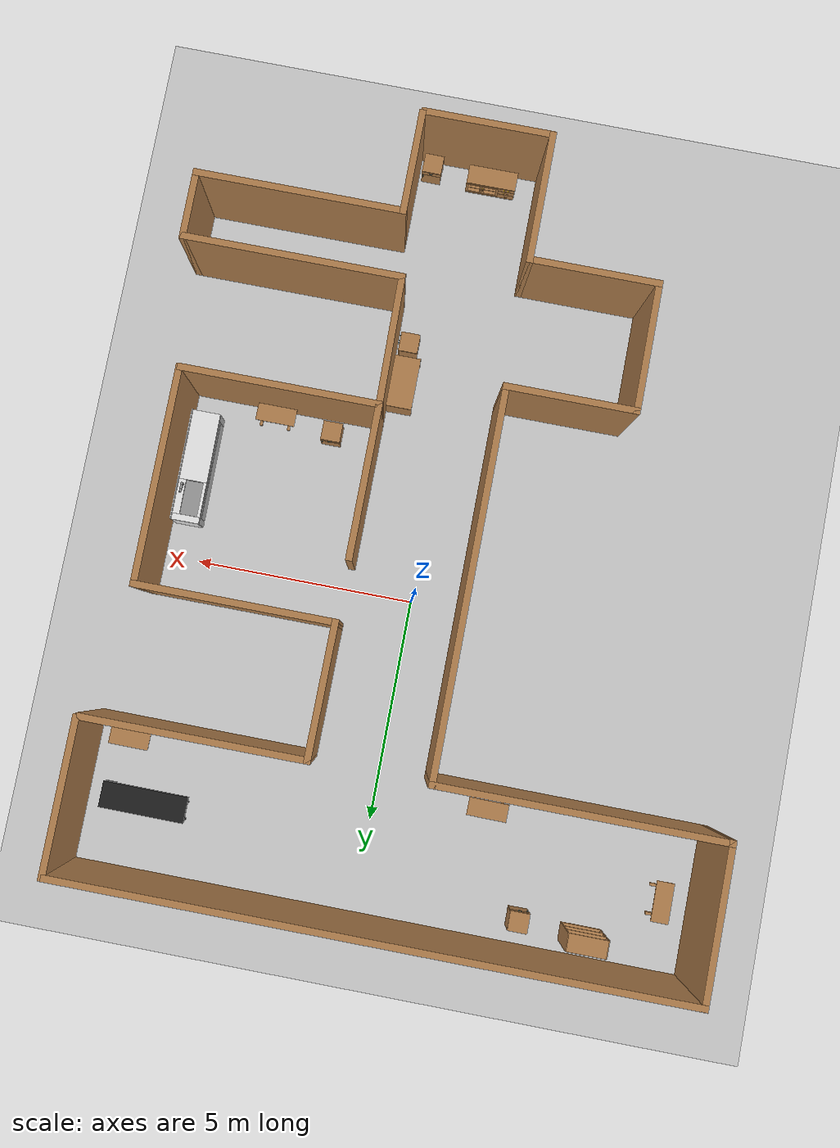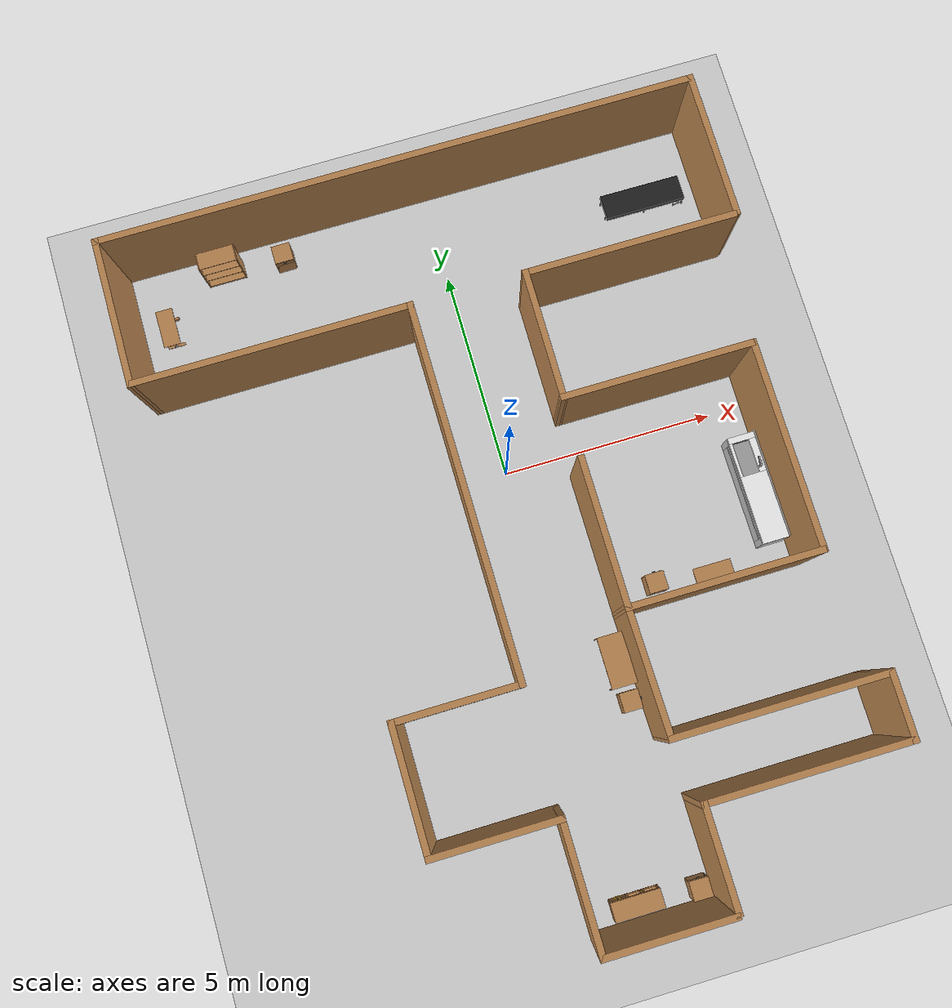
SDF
<sdf version="1.6">
 <world name="default">
  <light name="sun" type="directional">
   <pose>0 0 10 0 -0 0</pose>
   <diffuse>0.8 0.8 0.8 1</diffuse>
   <specular>0.2 0.2 0.2 1</specular>
   <attenuation>
    <range>1000</range>
    <constant>0.9</constant>
    <linear>0.01</linear>
    <quadratic>0.001</quadratic>
   </attenuation>
   <direction>-0.5 0.1 -0.9</direction>
  </light>
  <model name="ground_plane">
   <static>1</static>
   <link name="link">
    <collision name="collision">
     <geometry><plane><normal>0 0 1</normal><size>100 100</size></plane></geometry>
     <surface><friction><ode><mu>100</mu><mu2>50</mu2></ode></friction></surface>
    </collision>
    <visual name="visual">
     <cast_shadows>0</cast_shadows>
     <geometry><plane><normal>0 0 1</normal><size>100 100</size></plane></geometry>
     <material>
      <script><uri>file://media/materials/scripts/gazebo.material</uri><name>Gazebo/Grey</name></script>
     </material>
    </visual>
   </link>
  </model>
  <gravity>0 0 -9.8</gravity>
  <magnetic_field>6e-06 2.3e-05 -4.2e-05</magnetic_field>
  <atmosphere type="adiabatic"/>
  <physics name="default_physics" default="0" type="ode">
   <max_step_size>0.001</max_step_size>
   <real_time_factor>1</real_time_factor>
   <real_time_update_rate>1000</real_time_update_rate>
  </physics>
  <scene><ambient>0.4 0.4 0.4 1</ambient><background>0.7 0.7 0.7 1</background><shadows>1</shadows></scene>
  <audio><device>default</device></audio>
  <spherical_coordinates>
   <surface_model>EARTH_WGS84</surface_model>
   <latitude_deg>0</latitude_deg>
   <longitude_deg>0</longitude_deg>
   <elevation>0</elevation>
   <heading_deg>0</heading_deg>
  </spherical_coordinates>
  <model name="JUSTINAS_LAB3">
   <pose>-0.50094 -1.66418 0 0 -0 0</pose>
   <link name="Wall_102">
    <collision name="Wall_102_Collision">
     <geometry><box><size>6.5 0.15 2.5</size></box></geometry>
     <pose>0 0 1.25 0 -0 0</pose>
    </collision>
    <visual name="Wall_102_Visual">
     <pose>0 0 1.25 0 -0 0</pose>
     <geometry><box><size>6.5 0.15 2.5</size></box></geometry>
     <material>
      <script><uri>file://media/materials/scripts/gazebo.material</uri><name>Gazebo/Wood</name></script>
      <ambient>1 1 1 1</ambient>
     </material>
     <meta><layer>0</layer></meta>
    </visual>
    <pose>-3.78934 5.45538 0 0 -0 -6.2e-05</pose>
   </link>
   <link name="Wall_104">
    <collision name="Wall_104_Collision">
     <geometry><box><size>8.75 0.15 2.5</size></box></geometry>
     <pose>0 0 1.25 0 -0 0</pose>
    </collision>
    <visual name="Wall_104_Visual">
     <pose>0 0 1.25 0 -0 0</pose>
     <geometry><box><size>8.75 0.15 2.5</size></box></geometry>
     <material>
      <script><uri>file://media/materials/scripts/gazebo.material</uri><name>Gazebo/Wood</name></script>
      <ambient>1 1 1 1</ambient>
     </material>
     <meta><layer>0</layer></meta>
    </visual>
    <pose>-0.614387 1.15519 0 0 -0 -1.5708</pose>
   </link>
   <link name="Wall_106">
    <collision name="Wall_106_Collision">
     <geometry><box><size>3 0.15 2.5</size></box></geometry>
     <pose>0 0 1.25 0 -0 0</pose>
    </collision>
    <visual name="Wall_106_Visual">
     <pose>0 0 1.25 0 -0 0</pose>
     <geometry><box><size>3 0.15 2.5</size></box></geometry>
     <material>
      <script><uri>file://media/materials/scripts/gazebo.material</uri><name>Gazebo/Wood</name></script>
      <ambient>1 1 1 1</ambient>
     </material>
     <meta><layer>0</layer></meta>
    </visual>
    <pose>-2.03939 -3.14481 0 0 -0 3.14159</pose>
   </link>
   <link name="Wall_108">
    <collision name="Wall_108_Collision">
     <geometry><box><size>3 0.15 2.5</size></box></geometry>
     <pose>0 0 1.25 0 -0 0</pose>
    </collision>
    <visual name="Wall_108_Visual">
     <pose>0 0 1.25 0 -0 0</pose>
     <geometry><box><size>3 0.15 2.5</size></box></geometry>
     <material>
      <script><uri>file://media/materials/scripts/gazebo.material</uri><name>Gazebo/Wood</name></script>
      <ambient>1 1 1 1</ambient>
     </material>
     <meta><layer>0</layer></meta>
    </visual>
    <pose>-3.46439 -4.56981 0 0 -0 -1.5708</pose>
   </link>
   <link name="Wall_110">
    <collision name="Wall_110_Collision">
     <geometry><box><size>3 0.15 2.5</size></box></geometry>
     <pose>0 0 1.25 0 -0 0</pose>
    </collision>
    <visual name="Wall_110_Visual">
     <pose>0 0 1.25 0 -0 0</pose>
     <geometry><box><size>3 0.15 2.5</size></box></geometry>
     <material>
      <script><uri>file://media/materials/scripts/gazebo.material</uri><name>Gazebo/Wood</name></script>
      <ambient>1 1 1 1</ambient>
     </material>
     <meta><layer>0</layer></meta>
    </visual>
    <pose>-2.03939 -5.99481 0 0 -0 0</pose>
   </link>
   <link name="Wall_112">
    <collision name="Wall_112_Collision">
     <geometry><box><size>3 0.15 2.5</size></box></geometry>
     <pose>0 0 1.25 0 -0 0</pose>
    </collision>
    <visual name="Wall_112_Visual">
     <pose>0 0 1.25 0 -0 0</pose>
     <geometry><box><size>3 0.15 2.5</size></box></geometry>
     <material>
      <script><uri>file://media/materials/scripts/gazebo.material</uri><name>Gazebo/Wood</name></script>
      <ambient>1 1 1 1</ambient>
     </material>
     <meta><layer>0</layer></meta>
    </visual>
    <pose>-0.614387 -7.41981 0 0 -0 -1.5708</pose>
   </link>
   <link name="Wall_114">
    <collision name="Wall_114_Collision">
     <geometry><box><size>3 0.15 2.5</size></box></geometry>
     <pose>0 0 1.25 0 -0 0</pose>
    </collision>
    <visual name="Wall_114_Visual">
     <pose>0 0 1.25 0 -0 0</pose>
     <geometry><box><size>3 0.15 2.5</size></box></geometry>
     <material>
      <script><uri>file://media/materials/scripts/gazebo.material</uri><name>Gazebo/Wood</name></script>
      <ambient>1 1 1 1</ambient>
     </material>
     <meta><layer>0</layer></meta>
    </visual>
    <pose>0.810613 -8.84481 0 0 -0 0</pose>
   </link>
   <link name="Wall_116">
    <collision name="Wall_116_Collision">
     <geometry><box><size>3.53885 0.15 2.5</size></box></geometry>
     <pose>0 0 1.25 0 -0 0</pose>
    </collision>
    <visual name="Wall_116_Visual">
     <pose>0 0 1.25 0 -0 0</pose>
     <geometry><box><size>3.53885 0.15 2.5</size></box></geometry>
     <material>
      <script><uri>file://media/materials/scripts/gazebo.material</uri><name>Gazebo/Wood</name></script>
      <ambient>1 1 1 1</ambient>
     </material>
     <meta><layer>0</layer></meta>
    </visual>
    <pose>-6.95419 7.14997 0 0 -0 -1.57676</pose>
   </link>
   <link name="Wall_118">
    <collision name="Wall_118_Collision">
     <geometry><box><size>3.5 0.15 2.5</size></box></geometry>
     <pose>0 0 1.25 0 -0 0</pose>
    </collision>
    <visual name="Wall_118_Visual">
     <pose>0 0 1.25 0 -0 0</pose>
     <geometry><box><size>3.5 0.15 2.5</size></box></geometry>
     <material>
      <script><uri>file://media/materials/scripts/gazebo.material</uri><name>Gazebo/Wood</name></script>
      <ambient>1 1 1 1</ambient>
     </material>
     <meta><layer>0</layer></meta>
    </visual>
    <pose>6.96473 7.1669 0 0 -0 -1.5708</pose>
   </link>
   <link name="Wall_143">
    <collision name="Wall_143_Collision">
     <geometry><box><size>4.5 0.15 2.5</size></box></geometry>
     <pose>0 0 1.25 0 -0 0</pose>
    </collision>
    <visual name="Wall_143_Visual">
     <pose>0 0 1.25 0 -0 0</pose>
     <geometry><box><size>4.5 0.15 2.5</size></box></geometry>
     <material>
      <script><uri>file://media/materials/scripts/gazebo.material</uri><name>Gazebo/Wood</name></script>
      <ambient>1 1 1 1</ambient>
     </material>
     <meta><layer>0</layer></meta>
    </visual>
    <pose>4.1917 2.51558 0 0 -0 0</pose>
   </link>
   <link name="Wall_145">
    <collision name="Wall_145_Collision">
     <geometry><box><size>4.9 0.15 2.5</size></box></geometry>
     <pose>0 0 1.25 0 -0 0</pose>
    </collision>
    <visual name="Wall_145_Visual">
     <pose>0 0 1.25 0 -0 0</pose>
     <geometry><box><size>4.9 0.15 2.5</size></box></geometry>
     <material>
      <script><uri>file://media/materials/scripts/gazebo.material</uri><name>Gazebo/Wood</name></script>
      <ambient>1 1 1 1</ambient>
     </material>
     <meta><layer>0</layer></meta>
    </visual>
    <pose>6.3667 0.140581 0 0 -0 -1.5708</pose>
   </link>
   <link name="Wall_18">
    <collision name="Wall_18_Collision">
     <geometry><box><size>3.5 0.15 2.5</size></box></geometry>
     <pose>0 0 1.25 0 -0 0</pose>
    </collision>
    <visual name="Wall_18_Visual">
     <pose>0 0 1.25 0 -0 0</pose>
     <geometry><box><size>3.5 0.15 2.5</size></box></geometry>
     <material>
      <script><uri>file://media/materials/scripts/gazebo.material</uri><name>Gazebo/Wood</name></script>
      <ambient>1 1 1 1</ambient>
     </material>
     <meta><layer>0</layer></meta>
    </visual>
    <pose>1.99085 -0.569616 0 0 -0 1.5707</pose>
   </link>
   <link name="Wall_26">
    <collision name="Wall_26_Collision">
     <geometry><box><size>4.5 0.15 2.5</size></box></geometry>
     <pose>0 0 1.25 0 -0 0</pose>
    </collision>
    <visual name="Wall_26_Visual">
     <pose>0 0 1.25 0 -0 0</pose>
     <geometry><box><size>4.5 0.15 2.5</size></box></geometry>
     <material>
      <script><uri>file://media/materials/scripts/gazebo.material</uri><name>Gazebo/Wood</name></script>
      <ambient>1 1 1 1</ambient>
     </material>
     <meta><layer>0</layer></meta>
    </visual>
    <pose>4.1657 -2.24442 0 0 -0 0</pose>
   </link>
   <link name="Wall_32">
    <collision name="Wall_32_Collision">
     <geometry><box><size>3.08927 0.15 2.5</size></box></geometry>
     <pose>0 0 1.25 0 -0 0</pose>
    </collision>
    <visual name="Wall_32_Visual">
     <pose>0 0 1.25 0 -0 0</pose>
     <geometry><box><size>3.08927 0.15 2.5</size></box></geometry>
     <material>
      <script><uri>file://media/materials/scripts/gazebo.material</uri><name>Gazebo/Wood</name></script>
      <ambient>1 1 1 1</ambient>
     </material>
     <meta><layer>0</layer></meta>
    </visual>
    <pose>2.02616 3.98538 0 0 -0 1.56436</pose>
   </link>
   <link name="Wall_34">
    <collision name="Wall_34_Collision">
     <geometry><box><size>5 0.15 2.5</size></box></geometry>
     <pose>0 0 1.25 0 -0 0</pose>
    </collision>
    <visual name="Wall_34_Visual">
     <pose>0 0 1.25 0 -0 0</pose>
     <geometry><box><size>5 0.15 2.5</size></box></geometry>
     <material>
      <script><uri>file://media/materials/scripts/gazebo.material</uri><name>Gazebo/Wood</name></script>
      <ambient>1 1 1 1</ambient>
     </material>
     <meta><layer>0</layer></meta>
    </visual>
    <pose>4.46061 5.45519 0 0 -0 0</pose>
   </link>
   <link name="Wall_49">
    <collision name="Wall_49_Collision">
     <geometry><box><size>14.0588 0.15 2.5</size></box></geometry>
     <pose>0 0 1.25 0 -0 0</pose>
    </collision>
    <visual name="Wall_49_Visual">
     <pose>0 0 1.25 0 -0 0</pose>
     <geometry><box><size>14.0588 0.15 2.5</size></box></geometry>
     <material>
      <script><uri>file://media/materials/scripts/gazebo.material</uri><name>Gazebo/Wood</name></script>
      <ambient>1 1 1 1</ambient>
     </material>
     <meta><layer>0</layer></meta>
    </visual>
    <pose>0.010323 8.84313 0 0 -0 3.14141</pose>
   </link>
   <link name="Wall_65">
    <collision name="Wall_65_Collision">
     <geometry><box><size>3.00035 0.15 2.5</size></box></geometry>
     <pose>0 0 1.25 0 -0 0</pose>
    </collision>
    <visual name="Wall_65_Visual">
     <pose>0 0 1.25 0 -0 0</pose>
     <geometry><box><size>3.00035 0.15 2.5</size></box></geometry>
     <material>
      <script><uri>file://media/materials/scripts/gazebo.material</uri><name>Gazebo/Wood</name></script>
      <ambient>1 1 1 1</ambient>
     </material>
     <meta><layer>0</layer></meta>
    </visual>
    <pose>2.01316 -3.66962 0 0 -0 -1.55504</pose>
   </link>
   <link name="Wall_67">
    <collision name="Wall_67_Collision">
     <geometry><box><size>5 0.15 2.5</size></box></geometry>
     <pose>0 0 1.25 0 -0 0</pose>
    </collision>
    <visual name="Wall_67_Visual">
     <pose>0 0 1.25 0 -0 0</pose>
     <geometry><box><size>5 0.15 2.5</size></box></geometry>
     <material>
      <script><uri>file://media/materials/scripts/gazebo.material</uri><name>Gazebo/Wood</name></script>
      <ambient>1 1 1 1</ambient>
     </material>
     <meta><layer>0</layer></meta>
    </visual>
    <pose>4.46061 -5.09481 0 0 -0 0</pose>
   </link>
   <link name="Wall_69">
    <collision name="Wall_69_Collision">
     <geometry><box><size>1.6 0.15 2.5</size></box></geometry>
     <pose>0 0 1.25 0 -0 0</pose>
    </collision>
    <visual name="Wall_69_Visual">
     <pose>0 0 1.25 0 -0 0</pose>
     <geometry><box><size>1.6 0.15 2.5</size></box></geometry>
     <material>
      <script><uri>file://media/materials/scripts/gazebo.material</uri><name>Gazebo/Wood</name></script>
      <ambient>1 1 1 1</ambient>
     </material>
     <meta><layer>0</layer></meta>
    </visual>
    <pose>6.88561 -5.81981 0 0 -0 -1.5708</pose>
   </link>
   <link name="Wall_76">
    <collision name="Wall_76_Collision">
     <geometry><box><size>4.75 0.15 2.5</size></box></geometry>
     <pose>0 0 1.25 0 -0 0</pose>
    </collision>
    <visual name="Wall_76_Visual">
     <pose>0 0 1.25 0 -0 0</pose>
     <geometry><box><size>4.75 0.15 2.5</size></box></geometry>
     <material>
      <script><uri>file://media/materials/scripts/gazebo.material</uri><name>Gazebo/Wood</name></script>
      <ambient>1 1 1 1</ambient>
     </material>
     <meta><layer>0</layer></meta>
    </visual>
    <pose>4.58561 -6.54481 0 0 -0 3.14159</pose>
   </link>
   <link name="Wall_77">
    <collision name="Wall_77_Collision">
     <geometry><box><size>2.4 0.15 2.5</size></box></geometry>
     <pose>0 0 1.25 0 -0 0</pose>
    </collision>
    <visual name="Wall_77_Visual">
     <pose>0 0 1.25 0 -0 0</pose>
     <geometry><box><size>2.4 0.15 2.5</size></box></geometry>
     <material>
      <script><uri>file://media/materials/scripts/gazebo.material</uri><name>Gazebo/Wood</name></script>
      <ambient>1 1 1 1</ambient>
     </material>
     <meta><layer>0</layer></meta>
    </visual>
    <pose>2.28561 -7.66981 0 0 -0 -1.5708</pose>
   </link>
   <static>1</static>
  </model>
  <model name="bed">
   <link name="link">
    <inertial>
     <mass>10</mass>
     <inertia><ixx>1</ixx><ixy>0</ixy><ixz>0</ixz><iyy>1</iyy><iyz>0</iyz><izz>1</izz></inertia>
    </inertial>
    <visual name="cushion">
     <pose>-0.295 -0.975 0.2875 0 -0 0</pose>
     <geometry><box><size>0.59 1.95 0.095</size></box></geometry>
     <material>
      <script>
       <uri>model://base_materials/cloth/scripts</uri>
       <uri>model://base_materials/cloth/textures</uri>
       <name>cloth/black</name>
      </script>
     </material>
    </visual>
    <collision name="collision_cushion">
     <pose>-0.295 -0.975 0.2875 0 -0 0</pose>
     <geometry><box><size>0.59 1.95 0.095</size></box></geometry>
    </collision>
    <visual name="top_frame">
     <pose>-0.295 -0.975 0.225 0 -0 0</pose>
     <geometry><box><size>0.59 1.95 0.03</size></box></geometry>
     <material>
      <script><uri>model://base_materials/color/scripts</uri><name>hsr_color/grey</name></script>
     </material>
    </visual>
    <collision name="collision_top_frame">
     <pose>-0.295 -0.975 0.225 0 -0 0</pose>
     <geometry><box><size>0.59 1.95 0.03</size></box></geometry>
    </collision>
    <visual name="right_front_pole">
     <pose>-0.075 -0.0125 0.125 0 -0 0</pose>
     <geometry><cylinder><radius>0.0125</radius><length>0.17</length></cylinder></geometry>
     <material>
      <script><uri>model://base_materials/color/scripts</uri><name>hsr_color/grey</name></script>
     </material>
    </visual>
    <collision name="collision_right_front_pole">
     <pose>-0.075 -0.0125 0.125 0 -0 0</pose>
     <geometry><cylinder><radius>0.0125</radius><length>0.17</length></cylinder></geometry>
    </collision>
    <visual name="right_front_caster">
     <pose>-0.075 -0.0125 0.02 0 1.57 0</pose>
     <geometry><cylinder><radius>0.02</radius><length>0.04</length></cylinder></geometry>
     <material><script><name>Gazebo/Black</name><uri>__default__</uri></script></material>
    </visual>
    <collision name="collision_right_front_caster">
     <pose>-0.075 -0.0125 0.02 0 1.57 0</pose>
     <geometry><cylinder><radius>0.02</radius><length>0.04</length></cylinder></geometry>
    </collision>
    <visual name="right_back_pole">
     <pose>-0.46 -0.0125 0.125 0 -0 0</pose>
     <geometry><cylinder><radius>0.0125</radius><length>0.17</length></cylinder></geometry>
     <material>
      <script><uri>model://base_materials/color/scripts</uri><name>hsr_color/grey</name></script>
     </material>
    </visual>
    <collision name="collision_right_back_pole">
     <pose>-0.46 -0.0125 0.125 0 -0 0</pose>
     <geometry><cylinder><radius>0.0125</radius><length>0.17</length></cylinder></geometry>
    </collision>
    <visual name="right_back_caster">
     <pose>-0.46 -0.0125 0.02 0 1.57 0</pose>
     <geometry><cylinder><radius>0.02</radius><length>0.04</length></cylinder></geometry>
     <material><script><name>Gazebo/Black</name><uri>__default__</uri></script></material>
    </visual>
    <collision name="collision_back_front_caster">
     <pose>-0.46 -0.0125 0.02 0 1.57 0</pose>
     <geometry><cylinder><radius>0.02</radius><length>0.04</length></cylinder></geometry>
    </collision>
    <visual name="center_front_pole">
     <pose>-0.0425 -0.975 0.105 0 -0 0</pose>
     <geometry><cylinder><radius>0.0125</radius><length>0.21</length></cylinder></geometry>
     <material>
      <script><uri>model://base_materials/color/scripts</uri><name>hsr_color/grey</name></script>
     </material>
    </visual>
    <collision name="collision_center_front_pole">
     <pose>-0.0425 -0.975 0.105 0 -0 0</pose>
     <geometry><cylinder><radius>0.0125</radius><length>0.17</length></cylinder></geometry>
    </collision>
    <visual name="center_back_pole">
     <pose>-0.5475 -0.975 0.105 0 -0 0</pose>
     <geometry><cylinder><radius>0.0125</radius><length>0.21</length></cylinder></geometry>
     <material>
      <script><uri>model://base_materials/color/scripts</uri><name>hsr_color/grey</name></script>
     </material>
    </visual>
    <collision name="collision_center_back_pole">
     <pose>-0.5475 -0.975 0.105 0 -0 0</pose>
     <geometry><cylinder><radius>0.0125</radius><length>0.17</length></cylinder></geometry>
    </collision>
    <visual name="left_front_horizon_pole">
     <pose>-0.01 -1.825 0.06 1.57 -0 0</pose>
     <geometry><cylinder><radius>0.01</radius><length>0.25</length></cylinder></geometry>
     <material>
      <script><uri>model://base_materials/color/scripts</uri><name>hsr_color/grey</name></script>
     </material>
    </visual>
    <collision name="collision_left_front_horizon_pole">
     <pose>-0.01 -1.825 0.06 1.57 -0 0</pose>
     <geometry><cylinder><radius>0.01</radius><length>0.25</length></cylinder></geometry>
    </collision>
    <visual name="left_front_vertical_pole">
     <pose>-0.01 -1.825 0.14 0 -0 0</pose>
     <geometry><cylinder><radius>0.01</radius><length>0.14</length></cylinder></geometry>
     <material>
      <script><uri>model://base_materials/color/scripts</uri><name>hsr_color/grey</name></script>
     </material>
    </visual>
    <collision name="collision_left_front_vertical_pole">
     <pose>-0.01 -1.825 0.14 0 -0 0</pose>
     <geometry><cylinder><radius>0.01</radius><length>0.14</length></cylinder></geometry>
    </collision>
    <visual name="left_front_caster_r">
     <pose>-0.02 -1.725 0.025 0 1.57 0</pose>
     <geometry><cylinder><radius>0.025</radius><length>0.04</length></cylinder></geometry>
     <material><script><name>Gazebo/Black</name><uri>__default__</uri></script></material>
    </visual>
    <collision name="collision_left_front_caster_r">
     <pose>-0.02 -1.725 0.025 0 1.57 0</pose>
     <geometry><cylinder><radius>0.025</radius><length>0.04</length></cylinder></geometry>
    </collision>
    <visual name="left_front_caster_l">
     <pose>-0.02 -1.925 0.025 0 1.57 0</pose>
     <geometry><cylinder><radius>0.025</radius><length>0.04</length></cylinder></geometry>
     <material><script><name>Gazebo/Black</name><uri>__default__</uri></script></material>
    </visual>
    <collision name="collision_left_front_caster_l">
     <pose>-0.02 -1.925 0.025 0 1.57 0</pose>
     <geometry><cylinder><radius>0.025</radius><length>0.04</length></cylinder></geometry>
    </collision>
    <visual name="left_back_horizon_pole">
     <pose>-0.58 -1.825 0.06 1.57 -0 0</pose>
     <geometry><cylinder><radius>0.01</radius><length>0.25</length></cylinder></geometry>
     <material>
      <script><uri>model://base_materials/color/scripts</uri><name>hsr_color/grey</name></script>
     </material>
    </visual>
    <collision name="collision_left_back_horizon_pole">
     <pose>-0.58 -1.825 0.06 1.57 -0 0</pose>
     <geometry><cylinder><radius>0.01</radius><length>0.25</length></cylinder></geometry>
    </collision>
    <visual name="left_back_vertical_pole">
     <pose>-0.58 -1.825 0.14 0 -0 0</pose>
     <geometry><cylinder><radius>0.01</radius><length>0.14</length></cylinder></geometry>
     <material>
      <script><uri>model://base_materials/color/scripts</uri><name>hsr_color/grey</name></script>
     </material>
    </visual>
    <collision name="collision_left_back_vertical_pole">
     <pose>-0.58 -1.825 0.14 0 -0 0</pose>
     <geometry><cylinder><radius>0.01</radius><length>0.14</length></cylinder></geometry>
    </collision>
    <visual name="left_back_caster_r">
     <pose>-0.57 -1.725 0.025 0 1.57 0</pose>
     <geometry><cylinder><radius>0.025</radius><length>0.04</length></cylinder></geometry>
     <material><script><name>Gazebo/Black</name><uri>__default__</uri></script></material>
    </visual>
    <collision name="collision_left_back_caster_r">
     <pose>-0.57 -1.725 0.025 0 1.57 0</pose>
     <geometry><cylinder><radius>0.025</radius><length>0.04</length></cylinder></geometry>
    </collision>
    <visual name="left_back_caster_l">
     <pose>-0.57 -1.925 0.025 0 1.57 0</pose>
     <geometry><cylinder><radius>0.025</radius><length>0.04</length></cylinder></geometry>
     <material><script><name>Gazebo/Black</name><uri>__default__</uri></script></material>
    </visual>
    <collision name="collision_left_back_caster_l">
     <pose>-0.57 -1.925 0.025 0 1.57 0</pose>
     <geometry><cylinder><radius>0.025</radius><length>0.04</length></cylinder></geometry>
    </collision>
    <velocity_decay><linear>0</linear><angular>0</angular></velocity_decay>
   </link>
   <static>1</static>
   <pose>4.11326 5.87023 0 0 -0 1.56725</pose>
  </model>
  <model name="bed_table">
   <link name="link">
    <inertial>
     <pose>0 0.449 0.001 0 -0 0</pose>
     <mass>10</mass>
     <inertia><ixx>1</ixx><ixy>0</ixy><ixz>0</ixz><iyy>1</iyy><iyz>0</iyz><izz>1</izz></inertia>
    </inertial>
    <visual name="top_board">
     <pose>0 0.449 0.625 0 -0 0</pose>
     <geometry><box><size>0.398 0.898 0.02</size></box></geometry>
     <material>
      <script><uri>model://base_materials/wood/scripts/wood.material</uri><name>base_materials/wood</name></script>
     </material>
    </visual>
    <collision name="collision_top_board">
     <pose>0 0.449 0.625 0 -0 0</pose>
     <geometry><box><size>0.398 0.898 0.02</size></box></geometry>
    </collision>
    <visual name="right_pole">
     <pose>0 0.817 0.3515 0 -0 0</pose>
     <geometry><box><size>0.072 0.094 0.527</size></box></geometry>
     <material>
      <script><uri>model://base_materials/color/scripts</uri><name>hsr_color/grey</name></script>
     </material>
    </visual>
    <collision name="collision_right_pole">
     <pose>0 0.817 0.3515 0 -0 0</pose>
     <geometry><box><size>0.072 0.094 0.527</size></box></geometry>
    </collision>
    <visual name="right_bottom_pole">
     <pose>0 0.8225 0.044 0 -0 0</pose>
     <geometry><box><size>0.42 0.063 0.088</size></box></geometry>
     <material>
      <script><uri>model://base_materials/wood/scripts/wood.material</uri><name>base_materials/wood</name></script>
     </material>
    </visual>
    <collision name="collision_right_bottom_pole">
     <pose>0 0.8225 0.044 0 -0 0</pose>
     <geometry><box><size>0.42 0.063 0.088</size></box></geometry>
    </collision>
    <visual name="bottom_center_pole">
     <pose>0 0.502 0.03 0 -0 0</pose>
     <geometry><box><size>0.06 0.578 0.03</size></box></geometry>
     <material>
      <script><uri>model://base_materials/wood/scripts/wood.material</uri><name>base_materials/wood</name></script>
     </material>
    </visual>
    <collision name="collision_bottom_center_pole">
     <pose>0 0.502 0.03 0 -0 0</pose>
     <geometry><box><size>0.06 0.578 0.03</size></box></geometry>
    </collision>
    <visual name="left_bottom_pole">
     <pose>0 0.18 0.0325 0 -0 0</pose>
     <geometry><box><size>0.418 0.066 0.025</size></box></geometry>
     <material>
      <script><uri>model://base_materials/wood/scripts/wood.material</uri><name>base_materials/wood</name></script>
     </material>
    </visual>
    <collision name="collision_left_bottom_pole">
     <pose>0 0.18 0.0325 0 -0 0</pose>
     <geometry><box><size>0.418 0.066 0.025</size></box></geometry>
    </collision>
    <visual name="marker_0010">
     <pose>0 0.14 0.093 0 -0 0</pose>
     <geometry><box><size>0.09 0.001 0.09</size></box></geometry>
     <material>
      <script>
       <uri>model://bed_table/marker/0010/scripts</uri>
       <uri>model://bed_table/marker/0010/textures</uri>
       <name>Marker/0010</name>
      </script>
     </material>
    </visual>
    <collision name="collision_marker_0010">
     <pose>0 0.14 0.093 0 -0 0</pose>
     <geometry><box><size>0.09 0.001 0.09</size></box></geometry>
    </collision>
    <visual name="marker_0010_back_plate">
     <pose>0 0.146 0.093 0 -0 0</pose>
     <geometry><box><size>0.09 0.01 0.09</size></box></geometry>
     <material>
      <script><uri>model://base_materials/wood/scripts/wood.material</uri><name>base_materials/wood</name></script>
     </material>
    </visual>
    <collision name="collision_marker_0010_back_plate">
     <pose>0 0.146 0.093 0 -0 0</pose>
     <geometry><box><size>0.09 0.01 0.09</size></box></geometry>
    </collision>
    <velocity_decay><linear>0</linear><angular>0</angular></velocity_decay>
   </link>
   <static>1</static>
   <pose>5.1741 4.20126 0 0 0 -1.576</pose>
  </model>
  <model name="wagon">
   <link name="link">
    <inertial>
     <mass>10</mass>
     <inertia><ixx>1</ixx><ixy>0</ixy><ixz>0</ixz><iyy>1</iyy><iyz>0</iyz><izz>1</izz></inertia>
    </inertial>
    <visual name="left_board">
     <pose>-0.2325 0.01 0.345 0 -0 0</pose>
     <geometry><box><size>0.415 0.02 0.59</size></box></geometry>
     <material>
      <script><uri>model://base_materials/wood/scripts/wood.material</uri><name>base_materials/wood</name></script>
     </material>
    </visual>
    <collision name="collision_left_board">
     <pose>-0.2325 0.01 0.345 0 -0 0</pose>
     <geometry><box><size>0.415 0.02 0.59</size></box></geometry>
    </collision>
    <visual name="right_board">
     <pose>-0.2325 0.4325 0.345 0 -0 0</pose>
     <geometry><box><size>0.415 0.02 0.59</size></box></geometry>
     <material>
      <script><uri>model://base_materials/wood/scripts/wood.material</uri><name>base_materials/wood</name></script>
     </material>
    </visual>
    <collision name="collision_right_board">
     <pose>-0.2325 0.4325 0.345 0 -0 0</pose>
     <geometry><box><size>0.415 0.02 0.59</size></box></geometry>
    </collision>
    <visual name="top_board">
     <pose>-0.22 0.2225 0.655 0 -0 0</pose>
     <geometry><box><size>0.44 0.445 0.03</size></box></geometry>
     <material>
      <script><uri>model://base_materials/wood/scripts/wood.material</uri><name>base_materials/wood</name></script>
     </material>
    </visual>
    <collision name="collision_top_board">
     <pose>-0.22 0.2225 0.655 0 -0 0</pose>
     <geometry><box><size>0.44 0.445 0.03</size></box></geometry>
    </collision>
    <visual name="back_board">
     <pose>-0.425 0.2225 0.345 0 -0 0</pose>
     <geometry><box><size>0.02 0.405 0.59</size></box></geometry>
     <material>
      <script><uri>model://base_materials/wood/scripts/wood.material</uri><name>base_materials/wood</name></script>
     </material>
    </visual>
    <collision name="collision_back_board">
     <pose>-0.425 0.2225 0.345 0 -0 0</pose>
     <geometry><box><size>0.02 0.405 0.59</size></box></geometry>
    </collision>
    <visual name="bottom_board">
     <pose>-0.2325 0.2225 0.06 0 -0 0</pose>
     <geometry><box><size>0.415 0.405 0.02</size></box></geometry>
     <material>
      <script><uri>model://base_materials/wood/scripts/wood.material</uri><name>base_materials/wood</name></script>
     </material>
    </visual>
    <collision name="collision_bottom_board">
     <pose>-0.2325 0.2225 0.06 0 -0 0</pose>
     <geometry><box><size>0.415 0.405 0.02</size></box></geometry>
    </collision>
    <visual name="1st_drawer">
     <pose>-0.0125 0.2225 0.57 0 -0 0</pose>
     <geometry><box><size>0.025 0.445 0.14</size></box></geometry>
     <material>
      <script><uri>model://base_materials/wood/scripts/wood.material</uri><name>base_materials/wood</name></script>
     </material>
    </visual>
    <collision name="collision_1st_drawer">
     <pose>-0.0125 0.2225 0.57 0 -0 0</pose>
     <geometry><box><size>0.025 0.445 0.14</size></box></geometry>
    </collision>
    <visual name="1st_drawer_handle_l1">
     <pose>0.0115 0.1895 0.6 3.14159 1.57079 3.14159</pose>
     <geometry><cylinder><radius>0.007</radius><length>0.023</length></cylinder></geometry>
     <material>
      <ambient>0.18431 0.3098 0.3098 1</ambient>
      <diffuse>0.18431 0.3098 0.3098 1</diffuse>
      <specular>0.1 0.1 0.1 1</specular>
     </material>
    </visual>
    <collision name="collision_1st_drawer_handle_l1">
     <pose>0.0115 0.1895 0.6 3.14159 1.57079 3.14159</pose>
     <geometry><cylinder><radius>0.007</radius><length>0.023</length></cylinder></geometry>
    </collision>
    <visual name="1st_drawer_handle_l2">
     <pose>0.023 0.1895 0.6 0 -0 0</pose>
     <geometry><sphere><radius>0.007</radius></sphere></geometry>
     <material>
      <ambient>0.18431 0.3098 0.3098 1</ambient>
      <diffuse>0.18431 0.3098 0.3098 1</diffuse>
      <specular>0.1 0.1 0.1 1</specular>
     </material>
    </visual>
    <collision name="collision_1st_drawer_handle_l2">
     <pose>0.023 0.1895 0.6 0 -0 0</pose>
     <geometry><sphere><radius>0.007</radius></sphere></geometry>
    </collision>
    <visual name="1st_drawer_handle_r1">
     <pose>0.0115 0.2555 0.6 3.14159 1.57079 3.14159</pose>
     <geometry><cylinder><radius>0.007</radius><length>0.023</length></cylinder></geometry>
     <material>
      <ambient>0.18431 0.3098 0.3098 1</ambient>
      <diffuse>0.18431 0.3098 0.3098 1</diffuse>
      <specular>0.1 0.1 0.1 1</specular>
     </material>
    </visual>
    <collision name="collision_1st_drawer_handle_r1">
     <pose>0.0115 0.2555 0.6 3.14159 1.57079 3.14159</pose>
     <geometry><cylinder><radius>0.007</radius><length>0.023</length></cylinder></geometry>
    </collision>
    <visual name="1st_drawer_handle_r2">
     <pose>0.023 0.2555 0.6 0 -0 0</pose>
     <geometry><sphere><radius>0.007</radius></sphere></geometry>
     <material>
      <ambient>0.18431 0.3098 0.3098 1</ambient>
      <diffuse>0.18431 0.3098 0.3098 1</diffuse>
      <specular>0.1 0.1 0.1 1</specular>
     </material>
    </visual>
    <collision name="collision_1st_drawer_handle_r2">
     <pose>0.023 0.2555 0.6 0 -0 0</pose>
     <geometry><sphere><radius>0.007</radius></sphere></geometry>
    </collision>
    <visual name="1st_drawer_handle_center">
     <pose>0.023 0.2225 0.6 1.5708 -0 0</pose>
     <geometry><cylinder><radius>0.007</radius><length>0.066</length></cylinder></geometry>
     <material>
      <ambient>0.18431 0.3098 0.3098 1</ambient>
      <diffuse>0.18431 0.3098 0.3098 1</diffuse>
      <specular>0.1 0.1 0.1 1</specular>
     </material>
    </visual>
    <collision name="collision_1st_drawer_handle_center">
     <pose>0.023 0.2225 0.6 1.5708 -0 0</pose>
     <geometry><cylinder><radius>0.007</radius><length>0.066</length></cylinder></geometry>
    </collision>
    <visual name="2nd_drawer">
     <pose>-0.0125 0.2225 0.275 0 -0 0</pose>
     <geometry><box><size>0.025 0.445 0.45</size></box></geometry>
     <material>
      <script><uri>model://base_materials/wood/scripts/wood.material</uri><name>base_materials/wood</name></script>
     </material>
    </visual>
    <collision name="collision_2nd_drawer">
     <pose>-0.0125 0.2225 0.275 0 -0 0</pose>
     <geometry><box><size>0.025 0.445 0.45</size></box></geometry>
    </collision>
    <visual name="2nd_drawer_handle_top1">
     <pose>0.0115 0.04 0.47 3.14159 1.57079 3.14159</pose>
     <geometry><cylinder><radius>0.007</radius><length>0.023</length></cylinder></geometry>
     <material>
      <ambient>0.18431 0.3098 0.3098 1</ambient>
      <diffuse>0.18431 0.3098 0.3098 1</diffuse>
      <specular>0.1 0.1 0.1 1</specular>
     </material>
    </visual>
    <collision name="collision_2nd_drawer_handle_top1">
     <pose>0.0115 0.04 0.47 3.14159 1.57079 3.14159</pose>
     <geometry><cylinder><radius>0.007</radius><length>0.023</length></cylinder></geometry>
    </collision>
    <visual name="2nd_drawer_handle_top2">
     <pose>0.023 0.04 0.47 0 -0 0</pose>
     <geometry><sphere><radius>0.007</radius></sphere></geometry>
     <material>
      <ambient>0.18431 0.3098 0.3098 1</ambient>
      <diffuse>0.18431 0.3098 0.3098 1</diffuse>
      <specular>0.1 0.1 0.1 1</specular>
     </material>
    </visual>
    <collision name="2nd_drawer_handle_top2">
     <pose>0.023 0.04 0.47 0 -0 0</pose>
     <geometry><sphere><radius>0.007</radius></sphere></geometry>
    </collision>
    <visual name="2nd_drawer_handle_bottom1">
     <pose>0.0115 0.04 0.404 3.14159 1.57079 3.14159</pose>
     <geometry><cylinder><radius>0.007</radius><length>0.023</length></cylinder></geometry>
     <material>
      <ambient>0.18431 0.3098 0.3098 1</ambient>
      <diffuse>0.18431 0.3098 0.3098 1</diffuse>
      <specular>0.1 0.1 0.1 1</specular>
     </material>
    </visual>
    <collision name="collision_2nd_drawer_handle_bottom1">
     <pose>0.0115 0.04 0.404 3.14159 1.57079 3.14159</pose>
     <geometry><cylinder><radius>0.007</radius><length>0.023</length></cylinder></geometry>
    </collision>
    <visual name="2nd_drawer_handle_bottom2">
     <pose>0.023 0.04 0.404 0 -0 0</pose>
     <geometry><sphere><radius>0.007</radius></sphere></geometry>
     <material>
      <ambient>0.18431 0.3098 0.3098 1</ambient>
      <diffuse>0.18431 0.3098 0.3098 1</diffuse>
      <specular>0.1 0.1 0.1 1</specular>
     </material>
    </visual>
    <collision name="2nd_drawer_handle_bottom2">
     <pose>0.023 0.04 0.404 0 -0 0</pose>
     <geometry><sphere><radius>0.007</radius></sphere></geometry>
    </collision>
    <visual name="2nd_drawer_handle_center">
     <pose>0.023 0.04 0.437 0 -0 0</pose>
     <geometry><cylinder><radius>0.007</radius><length>0.066</length></cylinder></geometry>
     <material>
      <ambient>0.18431 0.3098 0.3098 1</ambient>
      <diffuse>0.18431 0.3098 0.3098 1</diffuse>
      <specular>0.1 0.1 0.1 1</specular>
     </material>
    </visual>
    <collision name="collision_2nd_drawer_handle_center">
     <pose>0.023 0.04 0.437 0 -0 0</pose>
     <geometry><cylinder><radius>0.007</radius><length>0.066</length></cylinder></geometry>
    </collision>
    <visual name="left_front_caster">
     <pose>-0.07 0.025 0.025 3.14159 1.57079 3.14159</pose>
     <geometry><cylinder><radius>0.025</radius><length>0.035</length></cylinder></geometry>
     <material><script><name>Gazebo/Black</name><uri>__default__</uri></script></material>
    </visual>
    <collision name="collision_left_front_caster">
     <pose>-0.07 0.025 0.025 3.14159 1.57079 3.14159</pose>
     <geometry><cylinder><radius>0.025</radius><length>0.035</length></cylinder></geometry>
    </collision>
    <visual name="right_front_caster">
     <pose>-0.07 0.42 0.025 3.14159 1.57079 3.14159</pose>
     <geometry><cylinder><radius>0.025</radius><length>0.035</length></cylinder></geometry>
     <material><script><name>Gazebo/Black</name><uri>__default__</uri></script></material>
    </visual>
    <collision name="collision_right_front_caster">
     <pose>-0.07 0.42 0.025 3.14159 1.57079 3.14159</pose>
     <geometry><cylinder><radius>0.025</radius><length>0.035</length></cylinder></geometry>
    </collision>
    <visual name="left_back_caster">
     <pose>-0.39 0.025 0.025 3.14159 1.57079 3.14159</pose>
     <geometry><cylinder><radius>0.025</radius><length>0.035</length></cylinder></geometry>
     <material><script><name>Gazebo/Black</name><uri>__default__</uri></script></material>
    </visual>
    <collision name="collision_left_back_caster">
     <pose>-0.39 0.025 0.025 3.14159 1.57079 3.14159</pose>
     <geometry><cylinder><radius>0.025</radius><length>0.035</length></cylinder></geometry>
    </collision>
    <visual name="right_back_caster">
     <pose>-0.39 0.42 0.025 3.14159 1.57079 3.14159</pose>
     <geometry><cylinder><radius>0.025</radius><length>0.035</length></cylinder></geometry>
     <material><script><name>Gazebo/Black</name><uri>__default__</uri></script></material>
    </visual>
    <collision name="collision_right_back_caster">
     <pose>-0.39 0.42 0.025 3.14159 1.57079 3.14159</pose>
     <geometry><cylinder><radius>0.025</radius><length>0.035</length></cylinder></geometry>
    </collision>
    <velocity_decay><linear>0</linear><angular>0</angular></velocity_decay>
   </link>
   <static>1</static>
   <pose>-3.86281 6.29786 0 0 0 -1.56746</pose>
  </model>
  <model name="bed_table_0">
   <link name="link">
    <inertial>
     <pose>0 0.449 0.001 0 -0 0</pose>
     <mass>10</mass>
     <inertia><ixx>1</ixx><ixy>0</ixy><ixz>0</ixz><iyy>1</iyy><iyz>0</iyz><izz>1</izz></inertia>
    </inertial>
    <visual name="top_board">
     <pose>0 0.449 0.625 0 -0 0</pose>
     <geometry><box><size>0.398 0.898 0.02</size></box></geometry>
     <material>
      <script><uri>model://base_materials/wood/scripts/wood.material</uri><name>base_materials/wood</name></script>
     </material>
    </visual>
    <collision name="collision_top_board">
     <pose>0 0.449 0.625 0 -0 0</pose>
     <geometry><box><size>0.398 0.898 0.02</size></box></geometry>
    </collision>
    <visual name="right_pole">
     <pose>0 0.817 0.3515 0 -0 0</pose>
     <geometry><box><size>0.072 0.094 0.527</size></box></geometry>
     <material>
      <script><uri>model://base_materials/color/scripts</uri><name>hsr_color/grey</name></script>
     </material>
    </visual>
    <collision name="collision_right_pole">
     <pose>0 0.817 0.3515 0 -0 0</pose>
     <geometry><box><size>0.072 0.094 0.527</size></box></geometry>
    </collision>
    <visual name="right_bottom_pole">
     <pose>0 0.8225 0.044 0 -0 0</pose>
     <geometry><box><size>0.42 0.063 0.088</size></box></geometry>
     <material>
      <script><uri>model://base_materials/wood/scripts/wood.material</uri><name>base_materials/wood</name></script>
     </material>
    </visual>
    <collision name="collision_right_bottom_pole">
     <pose>0 0.8225 0.044 0 -0 0</pose>
     <geometry><box><size>0.42 0.063 0.088</size></box></geometry>
    </collision>
    <visual name="bottom_center_pole">
     <pose>0 0.502 0.03 0 -0 0</pose>
     <geometry><box><size>0.06 0.578 0.03</size></box></geometry>
     <material>
      <script><uri>model://base_materials/wood/scripts/wood.material</uri><name>base_materials/wood</name></script>
     </material>
    </visual>
    <collision name="collision_bottom_center_pole">
     <pose>0 0.502 0.03 0 -0 0</pose>
     <geometry><box><size>0.06 0.578 0.03</size></box></geometry>
    </collision>
    <visual name="left_bottom_pole">
     <pose>0 0.18 0.0325 0 -0 0</pose>
     <geometry><box><size>0.418 0.066 0.025</size></box></geometry>
     <material>
      <script><uri>model://base_materials/wood/scripts/wood.material</uri><name>base_materials/wood</name></script>
     </material>
    </visual>
    <collision name="collision_left_bottom_pole">
     <pose>0 0.18 0.0325 0 -0 0</pose>
     <geometry><box><size>0.418 0.066 0.025</size></box></geometry>
    </collision>
    <visual name="marker_0010">
     <pose>0 0.14 0.093 0 -0 0</pose>
     <geometry><box><size>0.09 0.001 0.09</size></box></geometry>
     <material>
      <script>
       <uri>model://bed_table/marker/0010/scripts</uri>
       <uri>model://bed_table/marker/0010/textures</uri>
       <name>Marker/0010</name>
      </script>
     </material>
    </visual>
    <collision name="collision_marker_0010">
     <pose>0 0.14 0.093 0 -0 0</pose>
     <geometry><box><size>0.09 0.001 0.09</size></box></geometry>
    </collision>
    <visual name="marker_0010_back_plate">
     <pose>0 0.146 0.093 0 -0 0</pose>
     <geometry><box><size>0.09 0.01 0.09</size></box></geometry>
     <material>
      <script><uri>model://base_materials/wood/scripts/wood.material</uri><name>base_materials/wood</name></script>
     </material>
    </visual>
    <collision name="collision_marker_0010_back_plate">
     <pose>0 0.146 0.093 0 -0 0</pose>
     <geometry><box><size>0.09 0.01 0.09</size></box></geometry>
    </collision>
    <velocity_decay><linear>0</linear><angular>0</angular></velocity_decay>
   </link>
   <static>1</static>
   <pose>-6.69359 5.05597 0 0 -0 0</pose>
  </model>
  <model name="bed_table_1">
   <link name="link">
    <inertial>
     <pose>0 0.449 0.001 0 -0 0</pose>
     <mass>10</mass>
     <inertia><ixx>1</ixx><ixy>0</ixy><ixz>0</ixz><iyy>1</iyy><iyz>0</iyz><izz>1</izz></inertia>
    </inertial>
    <visual name="top_board">
     <pose>0 0.449 0.625 0 -0 0</pose>
     <geometry><box><size>0.398 0.898 0.02</size></box></geometry>
     <material>
      <script><uri>model://base_materials/wood/scripts/wood.material</uri><name>base_materials/wood</name></script>
     </material>
    </visual>
    <collision name="collision_top_board">
     <pose>0 0.449 0.625 0 -0 0</pose>
     <geometry><box><size>0.398 0.898 0.02</size></box></geometry>
    </collision>
    <visual name="right_pole">
     <pose>0 0.817 0.3515 0 -0 0</pose>
     <geometry><box><size>0.072 0.094 0.527</size></box></geometry>
     <material>
      <script><uri>model://base_materials/color/scripts</uri><name>hsr_color/grey</name></script>
     </material>
    </visual>
    <collision name="collision_right_pole">
     <pose>0 0.817 0.3515 0 -0 0</pose>
     <geometry><box><size>0.072 0.094 0.527</size></box></geometry>
    </collision>
    <visual name="right_bottom_pole">
     <pose>0 0.8225 0.044 0 -0 0</pose>
     <geometry><box><size>0.42 0.063 0.088</size></box></geometry>
     <material>
      <script><uri>model://base_materials/wood/scripts/wood.material</uri><name>base_materials/wood</name></script>
     </material>
    </visual>
    <collision name="collision_right_bottom_pole">
     <pose>0 0.8225 0.044 0 -0 0</pose>
     <geometry><box><size>0.42 0.063 0.088</size></box></geometry>
    </collision>
    <visual name="bottom_center_pole">
     <pose>0 0.502 0.03 0 -0 0</pose>
     <geometry><box><size>0.06 0.578 0.03</size></box></geometry>
     <material>
      <script><uri>model://base_materials/wood/scripts/wood.material</uri><name>base_materials/wood</name></script>
     </material>
    </visual>
    <collision name="collision_bottom_center_pole">
     <pose>0 0.502 0.03 0 -0 0</pose>
     <geometry><box><size>0.06 0.578 0.03</size></box></geometry>
    </collision>
    <visual name="left_bottom_pole">
     <pose>0 0.18 0.0325 0 -0 0</pose>
     <geometry><box><size>0.418 0.066 0.025</size></box></geometry>
     <material>
      <script><uri>model://base_materials/wood/scripts/wood.material</uri><name>base_materials/wood</name></script>
     </material>
    </visual>
    <collision name="collision_left_bottom_pole">
     <pose>0 0.18 0.0325 0 -0 0</pose>
     <geometry><box><size>0.418 0.066 0.025</size></box></geometry>
    </collision>
    <visual name="marker_0010">
     <pose>0 0.14 0.093 0 -0 0</pose>
     <geometry><box><size>0.09 0.001 0.09</size></box></geometry>
     <material>
      <script>
       <uri>model://bed_table/marker/0010/scripts</uri>
       <uri>model://bed_table/marker/0010/textures</uri>
       <name>Marker/0010</name>
      </script>
     </material>
    </visual>
    <collision name="collision_marker_0010">
     <pose>0 0.14 0.093 0 -0 0</pose>
     <geometry><box><size>0.09 0.001 0.09</size></box></geometry>
    </collision>
    <visual name="marker_0010_back_plate">
     <pose>0 0.146 0.093 0 -0 0</pose>
     <geometry><box><size>0.09 0.01 0.09</size></box></geometry>
     <material>
      <script><uri>model://base_materials/wood/scripts/wood.material</uri><name>base_materials/wood</name></script>
     </material>
    </visual>
    <collision name="collision_marker_0010_back_plate">
     <pose>0 0.146 0.093 0 -0 0</pose>
     <geometry><box><size>0.09 0.01 0.09</size></box></geometry>
    </collision>
    <velocity_decay><linear>0</linear><angular>0</angular></velocity_decay>
   </link>
   <static>1</static>
   <pose>-2.08388 4.24177 0 0 -0 1.55986</pose>
  </model>
  <model name="office_desk">
   <link name="link">
    <inertial>
     <mass>10</mass>
     <inertia><ixx>1</ixx><ixy>0</ixy><ixz>0</ixz><iyy>1</iyy><iyz>0</iyz><izz>1</izz></inertia>
    </inertial>
    <visual name="top_board">
     <pose>-0.3 0.6 0.69 0 -0 0</pose>
     <geometry><box><size>0.6 1.2 0.02</size></box></geometry>
     <material>
      <script>
       <uri>model://base_materials/wood/scripts/wood.material</uri>
       <name>base_materials/dark_wood</name>
      </script>
     </material>
    </visual>
    <collision name="collision_top_board">
     <pose>-0.3 0.6 0.69 0 -0 0</pose>
     <geometry><box><size>0.6 1.2 0.02</size></box></geometry>
    </collision>
    <visual name="left_board">
     <pose>-0.3 0.01 0.34 0 -0 0</pose>
     <geometry><box><size>0.6 0.02 0.68</size></box></geometry>
     <material>
      <script>
       <uri>model://base_materials/wood/scripts/wood.material</uri>
       <name>base_materials/dark_wood</name>
      </script>
     </material>
    </visual>
    <collision name="collision_left_board">
     <pose>-0.3 0.01 0.34 0 -0 0</pose>
     <geometry><box><size>0.6 0.02 0.68</size></box></geometry>
    </collision>
    <visual name="right_board">
     <pose>-0.3 1.19 0.34 0 -0 0</pose>
     <geometry><box><size>0.6 0.02 0.68</size></box></geometry>
     <material>
      <script>
       <uri>model://base_materials/wood/scripts/wood.material</uri>
       <name>base_materials/dark_wood</name>
      </script>
     </material>
    </visual>
    <collision name="collision_right_board">
     <pose>-0.3 1.19 0.34 0 -0 0</pose>
     <geometry><box><size>0.6 0.02 0.68</size></box></geometry>
    </collision>
    <visual name="center_board">
     <pose>-0.14 0.6 0.49 0 -0 0</pose>
     <geometry><box><size>0.02 1.16 0.4</size></box></geometry>
     <material>
      <script>
       <uri>model://base_materials/wood/scripts/wood.material</uri>
       <name>base_materials/dark_wood</name>
      </script>
     </material>
    </visual>
    <collision name="ollision_center_board">
     <pose>-0.14 0.6 0.49 0 -0 0</pose>
     <geometry><box><size>0.02 1.16 0.4</size></box></geometry>
    </collision>
    <velocity_decay><linear>0</linear><angular>0</angular></velocity_decay>
   </link>
   <static>1</static>
   <pose>1.42953 -5.49497 0 0 -0 0</pose>
  </model>
  <model name="bed_table_2">
   <link name="link">
    <inertial>
     <pose>0 0.449 0.001 0 -0 0</pose>
     <mass>10</mass>
     <inertia><ixx>1</ixx><ixy>0</ixy><ixz>0</ixz><iyy>1</iyy><iyz>0</iyz><izz>1</izz></inertia>
    </inertial>
    <visual name="top_board">
     <pose>0 0.449 0.625 0 -0 0</pose>
     <geometry><box><size>0.398 0.898 0.02</size></box></geometry>
     <material>
      <script><uri>model://base_materials/wood/scripts/wood.material</uri><name>base_materials/wood</name></script>
     </material>
    </visual>
    <collision name="collision_top_board">
     <pose>0 0.449 0.625 0 -0 0</pose>
     <geometry><box><size>0.398 0.898 0.02</size></box></geometry>
    </collision>
    <visual name="right_pole">
     <pose>0 0.817 0.3515 0 -0 0</pose>
     <geometry><box><size>0.072 0.094 0.527</size></box></geometry>
     <material>
      <script><uri>model://base_materials/color/scripts</uri><name>hsr_color/grey</name></script>
     </material>
    </visual>
    <collision name="collision_right_pole">
     <pose>0 0.817 0.3515 0 -0 0</pose>
     <geometry><box><size>0.072 0.094 0.527</size></box></geometry>
    </collision>
    <visual name="right_bottom_pole">
     <pose>0 0.8225 0.044 0 -0 0</pose>
     <geometry><box><size>0.42 0.063 0.088</size></box></geometry>
     <material>
      <script><uri>model://base_materials/wood/scripts/wood.material</uri><name>base_materials/wood</name></script>
     </material>
    </visual>
    <collision name="collision_right_bottom_pole">
     <pose>0 0.8225 0.044 0 -0 0</pose>
     <geometry><box><size>0.42 0.063 0.088</size></box></geometry>
    </collision>
    <visual name="bottom_center_pole">
     <pose>0 0.502 0.03 0 -0 0</pose>
     <geometry><box><size>0.06 0.578 0.03</size></box></geometry>
     <material>
      <script><uri>model://base_materials/wood/scripts/wood.material</uri><name>base_materials/wood</name></script>
     </material>
    </visual>
    <collision name="collision_bottom_center_pole">
     <pose>0 0.502 0.03 0 -0 0</pose>
     <geometry><box><size>0.06 0.578 0.03</size></box></geometry>
    </collision>
    <visual name="left_bottom_pole">
     <pose>0 0.18 0.0325 0 -0 0</pose>
     <geometry><box><size>0.418 0.066 0.025</size></box></geometry>
     <material>
      <script><uri>model://base_materials/wood/scripts/wood.material</uri><name>base_materials/wood</name></script>
     </material>
    </visual>
    <collision name="collision_left_bottom_pole">
     <pose>0 0.18 0.0325 0 -0 0</pose>
     <geometry><box><size>0.418 0.066 0.025</size></box></geometry>
    </collision>
    <visual name="marker_0010">
     <pose>0 0.14 0.093 0 -0 0</pose>
     <geometry><box><size>0.09 0.001 0.09</size></box></geometry>
     <material>
      <script>
       <uri>model://bed_table/marker/0010/scripts</uri>
       <uri>model://bed_table/marker/0010/textures</uri>
       <name>Marker/0010</name>
      </script>
     </material>
    </visual>
    <collision name="collision_marker_0010">
     <pose>0 0.14 0.093 0 -0 0</pose>
     <geometry><box><size>0.09 0.001 0.09</size></box></geometry>
    </collision>
    <visual name="marker_0010_back_plate">
     <pose>0 0.146 0.093 0 -0 0</pose>
     <geometry><box><size>0.09 0.01 0.09</size></box></geometry>
     <material>
      <script><uri>model://base_materials/wood/scripts/wood.material</uri><name>base_materials/wood</name></script>
     </material>
    </visual>
    <collision name="collision_marker_0010_back_plate">
     <pose>0 0.146 0.093 0 -0 0</pose>
     <geometry><box><size>0.09 0.01 0.09</size></box></geometry>
    </collision>
    <velocity_decay><linear>0</linear><angular>0</angular></velocity_decay>
   </link>
   <static>1</static>
   <pose>3.397 -3.61722 0 0 0 -1.57177</pose>
  </model>
  <model name="living_sideboard">
   <link name="link">
    <inertial>
     <mass>10</mass>
     <inertia><ixx>1</ixx><ixy>0</ixy><ixz>0</ixz><iyy>1</iyy><iyz>0</iyz><izz>1</izz></inertia>
    </inertial>
    <visual name="left_board">
     <pose>-0.23 0.01 0.3375 0 -0 0</pose>
     <geometry><box><size>0.42 0.02 0.495</size></box></geometry>
     <material>
      <script><uri>model://base_materials/wood/scripts/wood.material</uri><name>base_materials/wood</name></script>
     </material>
    </visual>
    <collision name="collision_left_board">
     <pose>-0.23 0.01 0.3375 0 -0 0</pose>
     <geometry><box><size>0.42 0.02 0.495</size></box></geometry>
    </collision>
    <visual name="back_board">
     <pose>-0.42 0.575 0.2925 0 -0 0</pose>
     <geometry><box><size>0.02 1.11 0.585</size></box></geometry>
     <material>
      <script><uri>model://base_materials/wood/scripts/wood.material</uri><name>base_materials/wood</name></script>
     </material>
    </visual>
    <collision name="collision_back_board">
     <pose>-0.42 0.575 0.2925 0 -0 0</pose>
     <geometry><box><size>0.02 1.11 0.585</size></box></geometry>
    </collision>
    <visual name="right_board">
     <pose>-0.23 1.14 0.3375 0 -0 0</pose>
     <geometry><box><size>0.42 0.02 0.495</size></box></geometry>
     <material>
      <script><uri>model://base_materials/wood/scripts/wood.material</uri><name>base_materials/wood</name></script>
     </material>
    </visual>
    <collision name="collision_right_board">
     <pose>-0.23 1.14 0.3375 0 -0 0</pose>
     <geometry><box><size>0.42 0.02 0.495</size></box></geometry>
    </collision>
    <visual name="center_vertical_board1">
     <pose>-0.23 0.74 0.3375 0 -0 0</pose>
     <geometry><box><size>0.42 0.02 0.495</size></box></geometry>
     <material>
      <script><uri>model://base_materials/wood/scripts/wood.material</uri><name>base_materials/wood</name></script>
     </material>
    </visual>
    <collision name="collision_center_vertical_board1">
     <pose>-0.23 0.74 0.3375 0 -0 0</pose>
     <geometry><box><size>0.42 0.02 0.495</size></box></geometry>
    </collision>
    <visual name="top_board">
     <pose>-0.22 0.575 0.6 0 -0 0</pose>
     <geometry><box><size>0.44 1.15 0.03</size></box></geometry>
     <material>
      <script><uri>model://base_materials/wood/scripts/wood.material</uri><name>base_materials/wood</name></script>
     </material>
    </visual>
    <collision name="collision_top_board">
     <pose>-0.22 0.575 0.6 0 -0 0</pose>
     <geometry><box><size>0.44 1.15 0.03</size></box></geometry>
    </collision>
    <visual name="bottom_board">
     <pose>-0.23 0.575 0.045 0 -0 0</pose>
     <geometry><box><size>0.42 1.15 0.09</size></box></geometry>
     <material>
      <script><uri>model://base_materials/wood/scripts/wood.material</uri><name>base_materials/wood</name></script>
     </material>
    </visual>
    <collision name="collision_bottom_board">
     <pose>-0.23 0.575 0.045 0 -0 0</pose>
     <geometry><box><size>0.42 1.15 0.09</size></box></geometry>
    </collision>
    <visual name="1st_shelf">
     <pose>-0.225 0.37 0.259 0 -0 0</pose>
     <geometry><box><size>0.36 0.72 0.018</size></box></geometry>
     <material>
      <script><uri>model://base_materials/wood/scripts/wood.material</uri><name>base_materials/wood</name></script>
     </material>
    </visual>
    <collision name="collision_1st_shelf">
     <pose>-0.225 0.37 0.259 0 -0 0</pose>
     <geometry><box><size>0.36 0.72 0.018</size></box></geometry>
    </collision>
    <visual name="2nd_shelf">
     <pose>-0.225 0.37 0.407 0 -0 0</pose>
     <geometry><box><size>0.36 0.72 0.018</size></box></geometry>
     <material>
      <script><uri>model://base_materials/wood/scripts/wood.material</uri><name>base_materials/wood</name></script>
     </material>
    </visual>
    <collision name="collision_2nd_shelf">
     <pose>-0.225 0.37 0.407 0 -0 0</pose>
     <geometry><box><size>0.36 0.72 0.018</size></box></geometry>
    </collision>
    <visual name="1st_drawer">
     <pose>-0.2025 0.95 0.52 0 -0 0</pose>
     <geometry><box><size>0.405 0.38 0.13</size></box></geometry>
     <material>
      <script><uri>model://base_materials/wood/scripts/wood.material</uri><name>base_materials/wood</name></script>
     </material>
    </visual>
    <collision name="collision_1st_drawer">
     <pose>-0.2025 0.95 0.52 0 -0 0</pose>
     <geometry><box><size>0.405 0.38 0.13</size></box></geometry>
    </collision>
    <visual name="1st_drawer_handle_l1">
     <pose>0.015 0.9015 0.535 3.14159 1.57079 3.14159</pose>
     <geometry><cylinder><radius>0.006</radius><length>0.03</length></cylinder></geometry>
     <material>
      <ambient>1 0.84314 0 1</ambient>
      <diffuse>1 0.84314 0 1</diffuse>
      <specular>0.1 0.1 0.1 1</specular>
     </material>
    </visual>
    <collision name="collision_1st_drawer_handle_l1">
     <pose>0.015 0.9015 0.535 3.14159 1.57079 3.14159</pose>
     <geometry><cylinder><radius>0.006</radius><length>0.03</length></cylinder></geometry>
    </collision>
    <visual name="1st_drawer_handle_l2">
     <pose>0.03 0.9015 0.535 0 -0 0</pose>
     <geometry><sphere><radius>0.006</radius></sphere></geometry>
     <material>
      <ambient>1 0.84314 0 1</ambient>
      <diffuse>1 0.84314 0 1</diffuse>
      <specular>0.1 0.1 0.1 1</specular>
     </material>
    </visual>
    <collision name="collision_1st_drawer_handle_l2">
     <pose>0.03 0.9015 0.535 0 -0 0</pose>
     <geometry><sphere><radius>0.006</radius></sphere></geometry>
    </collision>
    <visual name="1st_drawer_handle_r1">
     <pose>0.015 0.9985 0.535 3.14159 1.57079 3.14159</pose>
     <geometry><cylinder><radius>0.006</radius><length>0.03</length></cylinder></geometry>
     <material>
      <ambient>1 0.84314 0 1</ambient>
      <diffuse>1 0.84314 0 1</diffuse>
      <specular>0.1 0.1 0.1 1</specular>
     </material>
    </visual>
    <collision name="collision_1st_drawer_handle_r1">
     <pose>0.015 0.9985 0.535 3.14159 1.57079 3.14159</pose>
     <geometry><cylinder><radius>0.006</radius><length>0.03</length></cylinder></geometry>
    </collision>
    <visual name="1st_drawer_handle_r2">
     <pose>0.03 0.9985 0.535 0 -0 0</pose>
     <geometry><sphere><radius>0.006</radius></sphere></geometry>
     <material>
      <ambient>1 0.84314 0 1</ambient>
      <diffuse>1 0.84314 0 1</diffuse>
      <specular>0.1 0.1 0.1 1</specular>
     </material>
    </visual>
    <collision name="collision_1st_drawer_handle_r2">
     <pose>0.03 0.9985 0.535 0 -0 0</pose>
     <geometry><sphere><radius>0.006</radius></sphere></geometry>
    </collision>
    <visual name="1st_drawer_handle_center">
     <pose>0.03 0.95 0.535 1.5708 -0 0</pose>
     <geometry><cylinder><radius>0.006</radius><length>0.097</length></cylinder></geometry>
     <material>
      <script><uri>model://base_materials/wood/scripts/wood.material</uri><name>base_materials/wood</name></script>
     </material>
    </visual>
    <collision name="collision_1st_drawer_handle_center">
     <pose>0.03 0.95 0.535 1.5708 -0 0</pose>
     <geometry><cylinder><radius>0.006</radius><length>0.097</length></cylinder></geometry>
    </collision>
    <visual name="2nd_drawer">
     <pose>-0.2025 0.95 0.37 0 -0 0</pose>
     <geometry><box><size>0.405 0.38 0.17</size></box></geometry>
     <material>
      <script><uri>model://base_materials/wood/scripts/wood.material</uri><name>base_materials/wood</name></script>
     </material>
    </visual>
    <collision name="collision_2nd_drawer">
     <pose>-0.2025 0.95 0.37 0 -0 0</pose>
     <geometry><box><size>0.405 0.38 0.17</size></box></geometry>
    </collision>
    <visual name="2nd_drawer_handle_l1">
     <pose>0.015 0.9015 0.405 3.14159 1.57079 3.14159</pose>
     <geometry><cylinder><radius>0.006</radius><length>0.03</length></cylinder></geometry>
     <material>
      <ambient>1 0.84314 0 1</ambient>
      <diffuse>1 0.84314 0 1</diffuse>
      <specular>0.1 0.1 0.1 1</specular>
     </material>
    </visual>
    <collision name="collision_2nd_drawer_handle_l1">
     <pose>0.015 0.9015 0.405 3.14159 1.57079 3.14159</pose>
     <geometry><cylinder><radius>0.006</radius><length>0.03</length></cylinder></geometry>
    </collision>
    <visual name="2nd_drawer_handle_l2">
     <pose>0.03 0.9015 0.405 0 -0 0</pose>
     <geometry><sphere><radius>0.006</radius></sphere></geometry>
     <material>
      <ambient>1 0.84314 0 1</ambient>
      <diffuse>1 0.84314 0 1</diffuse>
      <specular>0.1 0.1 0.1 1</specular>
     </material>
    </visual>
    <collision name="collision_2nd_drawer_handle_l2">
     <pose>0.03 0.9015 0.405 0 -0 0</pose>
     <geometry><sphere><radius>0.006</radius></sphere></geometry>
    </collision>
    <visual name="2nd_drawer_handle_r1">
     <pose>0.015 0.9985 0.405 3.14159 1.57079 3.14159</pose>
     <geometry><cylinder><radius>0.006</radius><length>0.03</length></cylinder></geometry>
     <material>
      <ambient>1 0.84314 0 1</ambient>
      <diffuse>1 0.84314 0 1</diffuse>
      <specular>0.1 0.1 0.1 1</specular>
     </material>
    </visual>
    <collision name="collision_2nd_drawer_handle_r1">
     <pose>0.015 0.9985 0.405 3.14159 1.57079 3.14159</pose>
     <geometry><cylinder><radius>0.006</radius><length>0.03</length></cylinder></geometry>
    </collision>
    <visual name="2nd_drawer_handle_r2">
     <pose>0.03 0.9985 0.405 0 -0 0</pose>
     <geometry><sphere><radius>0.006</radius></sphere></geometry>
     <material>
      <ambient>1 0.84314 0 1</ambient>
      <diffuse>1 0.84314 0 1</diffuse>
      <specular>0.1 0.1 0.1 1</specular>
     </material>
    </visual>
    <collision name="collision_2nd_drawer_handle_r2">
     <pose>0.03 0.9985 0.405 0 -0 0</pose>
     <geometry><sphere><radius>0.006</radius></sphere></geometry>
    </collision>
    <visual name="2nd_drawer_handle_center">
     <pose>0.03 0.95 0.405 1.5708 -0 0</pose>
     <geometry><cylinder><radius>0.006</radius><length>0.097</length></cylinder></geometry>
     <material>
      <script><uri>model://base_materials/wood/scripts/wood.material</uri><name>base_materials/wood</name></script>
     </material>
    </visual>
    <collision name="collision_2nd_drawer_handle_center">
     <pose>0.03 0.95 0.405 1.5708 -0 0</pose>
     <geometry><cylinder><radius>0.006</radius><length>0.097</length></cylinder></geometry>
    </collision>
    <visual name="3rd_drawer">
     <pose>-0.2025 0.95 0.18 0 -0 0</pose>
     <geometry><box><size>0.405 0.38 0.21</size></box></geometry>
     <material>
      <script><uri>model://base_materials/wood/scripts/wood.material</uri><name>base_materials/wood</name></script>
     </material>
    </visual>
    <collision name="collision_3rd_drawer">
     <pose>-0.2025 0.95 0.18 0 -0 0</pose>
     <geometry><box><size>0.405 0.38 0.21</size></box></geometry>
    </collision>
    <visual name="3rd_drawer_handle_l1">
     <pose>0.015 0.9015 0.235 3.14159 1.57079 3.14159</pose>
     <geometry><cylinder><radius>0.006</radius><length>0.03</length></cylinder></geometry>
     <material>
      <ambient>1 0.84314 0 1</ambient>
      <diffuse>1 0.84314 0 1</diffuse>
      <specular>0.1 0.1 0.1 1</specular>
     </material>
    </visual>
    <collision name="collision_3rd_drawer_handle_l1">
     <pose>0.015 0.9015 0.235 3.14159 1.57079 3.14159</pose>
     <geometry><cylinder><radius>0.006</radius><length>0.03</length></cylinder></geometry>
    </collision>
    <visual name="3rd_drawer_handle_l2">
     <pose>0.03 0.9015 0.235 0 -0 0</pose>
     <geometry><sphere><radius>0.006</radius></sphere></geometry>
     <material>
      <ambient>1 0.84314 0 1</ambient>
      <diffuse>1 0.84314 0 1</diffuse>
      <specular>0.1 0.1 0.1 1</specular>
     </material>
    </visual>
    <collision name="collision_3rd_drawer_handle_l2">
     <pose>0.03 0.9015 0.235 0 -0 0</pose>
     <geometry><sphere><radius>0.006</radius></sphere></geometry>
    </collision>
    <visual name="3rd_drawer_handle_r1">
     <pose>0.015 0.9985 0.235 3.14159 1.57079 3.14159</pose>
     <geometry><cylinder><radius>0.006</radius><length>0.03</length></cylinder></geometry>
     <material>
      <ambient>1 0.84314 0 1</ambient>
      <diffuse>1 0.84314 0 1</diffuse>
      <specular>0.1 0.1 0.1 1</specular>
     </material>
    </visual>
    <collision name="collision_3rd_drawer_handle_r1">
     <pose>0.015 0.9985 0.235 3.14159 1.57079 3.14159</pose>
     <geometry><cylinder><radius>0.006</radius><length>0.03</length></cylinder></geometry>
    </collision>
    <visual name="3rd_drawer_handle_r2">
     <pose>0.03 0.9985 0.235 0 -0 0</pose>
     <geometry><sphere><radius>0.006</radius></sphere></geometry>
     <material>
      <ambient>1 0.84314 0 1</ambient>
      <diffuse>1 0.84314 0 1</diffuse>
      <specular>0.1 0.1 0.1 1</specular>
     </material>
    </visual>
    <collision name="collision_3rd_drawer_handle_r2">
     <pose>0.03 0.9985 0.235 0 -0 0</pose>
     <geometry><sphere><radius>0.006</radius></sphere></geometry>
    </collision>
    <visual name="3rd_drawer_handle_center">
     <pose>0.03 0.95 0.235 1.5708 -0 0</pose>
     <geometry><cylinder><radius>0.006</radius><length>0.097</length></cylinder></geometry>
     <material>
      <script><uri>model://base_materials/wood/scripts/wood.material</uri><name>base_materials/wood</name></script>
     </material>
    </visual>
    <collision name="collision_3rd_drawer_handle_center">
     <pose>0.03 0.95 0.235 1.5708 -0 0</pose>
     <geometry><cylinder><radius>0.006</radius><length>0.097</length></cylinder></geometry>
    </collision>
    <visual name="left_door_left_frame">
     <pose>-0.01 0.025 0.3275 0 -0 0</pose>
     <geometry><box><size>0.02 0.05 0.405</size></box></geometry>
     <material>
      <script><uri>model://base_materials/wood/scripts/wood.material</uri><name>base_materials/wood</name></script>
     </material>
    </visual>
    <collision name="collision_left_door_left_frame">
     <pose>-0.01 0.025 0.3275 0 -0 0</pose>
     <geometry><box><size>0.02 0.05 0.405</size></box></geometry>
    </collision>
    <visual name="left_door_right_frame">
     <pose>-0.01 0.355 0.3275 0 -0 0</pose>
     <geometry><box><size>0.02 0.05 0.405</size></box></geometry>
     <material>
      <script><uri>model://base_materials/wood/scripts/wood.material</uri><name>base_materials/wood</name></script>
     </material>
    </visual>
    <collision name="collision_left_door_right_frame">
     <pose>-0.01 0.355 0.3275 0 -0 0</pose>
     <geometry><box><size>0.02 0.05 0.405</size></box></geometry>
    </collision>
    <visual name="left_door_handle_top1">
     <pose>0.015 0.355 0.4475 3.14159 1.57079 3.14159</pose>
     <geometry><cylinder><radius>0.006</radius><length>0.03</length></cylinder></geometry>
     <material>
      <ambient>1 0.84314 0 1</ambient>
      <diffuse>1 0.84314 0 1</diffuse>
      <specular>0.1 0.1 0.1 1</specular>
     </material>
    </visual>
    <collision name="collision_left_door_handle_top1">
     <pose>0.015 0.355 0.4475 3.14159 1.57079 3.14159</pose>
     <geometry><cylinder><radius>0.006</radius><length>0.03</length></cylinder></geometry>
    </collision>
    <visual name="left_door_handle_top2">
     <pose>0.03 0.355 0.4475 0 -0 0</pose>
     <geometry><sphere><radius>0.006</radius></sphere></geometry>
     <material>
      <ambient>1 0.84314 0 1</ambient>
      <diffuse>1 0.84314 0 1</diffuse>
      <specular>0.1 0.1 0.1 1</specular>
     </material>
    </visual>
    <collision name="collision_left_door_handle_top2">
     <pose>0.03 0.355 0.4475 0 -0 0</pose>
     <geometry><sphere><radius>0.006</radius></sphere></geometry>
    </collision>
    <visual name="left_door_handle_bottom1">
     <pose>0.015 0.355 0.3505 3.14159 1.57079 3.14159</pose>
     <geometry><cylinder><radius>0.006</radius><length>0.03</length></cylinder></geometry>
     <material>
      <ambient>1 0.84314 0 1</ambient>
      <diffuse>1 0.84314 0 1</diffuse>
      <specular>0.1 0.1 0.1 1</specular>
     </material>
    </visual>
    <collision name="collision_left_door_handle_bottom1">
     <pose>0.015 0.355 0.3505 3.14159 1.57079 3.14159</pose>
     <geometry><cylinder><radius>0.006</radius><length>0.03</length></cylinder></geometry>
    </collision>
    <visual name="left_door_handle_bottom2">
     <pose>0.03 0.355 0.3505 0 -0 0</pose>
     <geometry><sphere><radius>0.006</radius></sphere></geometry>
     <material>
      <ambient>1 0.84314 0 1</ambient>
      <diffuse>1 0.84314 0 1</diffuse>
      <specular>0.1 0.1 0.1 1</specular>
     </material>
    </visual>
    <collision name="collision_left_door_handle_bottom2">
     <pose>0.03 0.355 0.3505 0 -0 0</pose>
     <geometry><sphere><radius>0.006</radius></sphere></geometry>
    </collision>
    <visual name="left_door_handle_center">
     <pose>0.03 0.355 0.399 0 -0 0</pose>
     <geometry><cylinder><radius>0.006</radius><length>0.097</length></cylinder></geometry>
     <material>
      <script><uri>model://base_materials/wood/scripts/wood.material</uri><name>base_materials/wood</name></script>
     </material>
    </visual>
    <collision name="collision_left_door_handle_center">
     <pose>0.03 0.355 0.399 0 -0 0</pose>
     <geometry><cylinder><radius>0.006</radius><length>0.097</length></cylinder></geometry>
    </collision>
    <visual name="left_door_top_frame">
     <pose>-0.01 0.19 0.5575 0 -0 0</pose>
     <geometry><box><size>0.02 0.38 0.055</size></box></geometry>
     <material>
      <script><uri>model://base_materials/wood/scripts/wood.material</uri><name>base_materials/wood</name></script>
     </material>
    </visual>
    <collision name="collision_left_door_top_frame">
     <pose>-0.01 0.19 0.5575 0 -0 0</pose>
     <geometry><box><size>0.02 0.38 0.055</size></box></geometry>
    </collision>
    <visual name="left_door_bottom_frame">
     <pose>-0.01 0.19 0.1 0 -0 0</pose>
     <geometry><box><size>0.02 0.38 0.05</size></box></geometry>
     <material>
      <script><uri>model://base_materials/wood/scripts/wood.material</uri><name>base_materials/wood</name></script>
     </material>
    </visual>
    <collision name="collision_left_door_bottom_frame">
     <pose>-0.01 0.19 0.1 0 -0 0</pose>
     <geometry><box><size>0.02 0.38 0.05</size></box></geometry>
    </collision>
    <visual name="right_door_left_frame">
     <pose>-0.01 0.405 0.3275 0 -0 0</pose>
     <geometry><box><size>0.02 0.05 0.405</size></box></geometry>
     <material>
      <script><uri>model://base_materials/wood/scripts/wood.material</uri><name>base_materials/wood</name></script>
     </material>
    </visual>
    <collision name="collision_right_door_left_frame">
     <pose>-0.01 0.405 0.3275 0 -0 0</pose>
     <geometry><box><size>0.02 0.05 0.405</size></box></geometry>
    </collision>
    <visual name="right_door_right_frame">
     <pose>-0.01 0.735 0.3275 0 -0 0</pose>
     <geometry><box><size>0.02 0.05 0.405</size></box></geometry>
     <material>
      <script><uri>model://base_materials/wood/scripts/wood.material</uri><name>base_materials/wood</name></script>
     </material>
    </visual>
    <collision name="collision_right_door_right_frame">
     <pose>-0.01 0.735 0.3275 0 -0 0</pose>
     <geometry><box><size>0.02 0.05 0.405</size></box></geometry>
    </collision>
    <visual name="right_door_top_frame">
     <pose>-0.01 0.57 0.5575 0 -0 0</pose>
     <geometry><box><size>0.02 0.38 0.055</size></box></geometry>
     <material>
      <script><uri>model://base_materials/wood/scripts/wood.material</uri><name>base_materials/wood</name></script>
     </material>
    </visual>
    <collision name="collision_right_door_top_frame">
     <pose>-0.01 0.57 0.5575 0 -0 0</pose>
     <geometry><box><size>0.02 0.38 0.055</size></box></geometry>
    </collision>
    <visual name="right_door_bottom_frame">
     <pose>-0.01 0.57 0.1 0 -0 0</pose>
     <geometry><box><size>0.02 0.38 0.05</size></box></geometry>
     <material>
      <script><uri>model://base_materials/wood/scripts/wood.material</uri><name>base_materials/wood</name></script>
     </material>
    </visual>
    <collision name="collision_right_door_bottom_frame">
     <pose>-0.01 0.57 0.1 0 -0 0</pose>
     <geometry><box><size>0.02 0.38 0.05</size></box></geometry>
    </collision>
    <visual name="right_door_handle_top1">
     <pose>0.015 0.405 0.4475 3.14159 1.57079 3.14159</pose>
     <geometry><cylinder><radius>0.006</radius><length>0.03</length></cylinder></geometry>
     <material>
      <ambient>1 0.84314 0 1</ambient>
      <diffuse>1 0.84314 0 1</diffuse>
      <specular>0.1 0.1 0.1 1</specular>
     </material>
    </visual>
    <collision name="collision_right_door_handle_top1">
     <pose>0.015 0.405 0.4475 3.14159 1.57079 3.14159</pose>
     <geometry><cylinder><radius>0.006</radius><length>0.03</length></cylinder></geometry>
    </collision>
    <visual name="right_door_handle_top2">
     <pose>0.03 0.405 0.4475 0 -0 0</pose>
     <geometry><sphere><radius>0.006</radius></sphere></geometry>
     <material>
      <ambient>1 0.84314 0 1</ambient>
      <diffuse>1 0.84314 0 1</diffuse>
      <specular>0.1 0.1 0.1 1</specular>
     </material>
    </visual>
    <collision name="collision_right_door_handle_top2">
     <pose>0.03 0.405 0.4475 0 -0 0</pose>
     <geometry><sphere><radius>0.006</radius></sphere></geometry>
    </collision>
    <visual name="right_door_handle_bottom1">
     <pose>0.015 0.405 0.3505 3.14159 1.57079 3.14159</pose>
     <geometry><cylinder><radius>0.006</radius><length>0.03</length></cylinder></geometry>
     <material>
      <ambient>1 0.84314 0 1</ambient>
      <diffuse>1 0.84314 0 1</diffuse>
      <specular>0.1 0.1 0.1 1</specular>
     </material>
    </visual>
    <collision name="collision_right_door_handle_bottom1">
     <pose>0.015 0.405 0.3505 3.14159 1.57079 3.14159</pose>
     <geometry><cylinder><radius>0.006</radius><length>0.03</length></cylinder></geometry>
    </collision>
    <visual name="right_door_handle_bottom2">
     <pose>0.03 0.405 0.3505 0 -0 0</pose>
     <geometry><sphere><radius>0.006</radius></sphere></geometry>
     <material>
      <ambient>1 0.84314 0 1</ambient>
      <diffuse>1 0.84314 0 1</diffuse>
      <specular>0.1 0.1 0.1 1</specular>
     </material>
    </visual>
    <collision name="collision_right_door_handle_bottom2">
     <pose>0.03 0.405 0.3505 0 -0 0</pose>
     <geometry><sphere><radius>0.006</radius></sphere></geometry>
    </collision>
    <visual name="right_door_handle_center">
     <pose>0.03 0.405 0.399 0 -0 0</pose>
     <geometry><cylinder><radius>0.006</radius><length>0.097</length></cylinder></geometry>
     <material>
      <script><uri>model://base_materials/wood/scripts/wood.material</uri><name>base_materials/wood</name></script>
     </material>
    </visual>
    <collision name="collision_right_door_handle_center">
     <pose>0.03 0.4 0.399 0 -0 0</pose>
     <geometry><cylinder><radius>0.006</radius><length>0.097</length></cylinder></geometry>
    </collision>
    <velocity_decay><linear>0</linear><angular>0</angular></velocity_decay>
   </link>
   <static>1</static>
   <pose>0.568188 -9.86074 0 0 -0 1.5725</pose>
  </model>
  <model name="wagon_0">
   <link name="link">
    <inertial>
     <mass>10</mass>
     <inertia><ixx>1</ixx><ixy>0</ixy><ixz>0</ixz><iyy>1</iyy><iyz>0</iyz><izz>1</izz></inertia>
    </inertial>
    <visual name="left_board">
     <pose>-0.2325 0.01 0.345 0 -0 0</pose>
     <geometry><box><size>0.415 0.02 0.59</size></box></geometry>
     <material>
      <script><uri>model://base_materials/wood/scripts/wood.material</uri><name>base_materials/wood</name></script>
     </material>
    </visual>
    <collision name="collision_left_board">
     <pose>-0.2325 0.01 0.345 0 -0 0</pose>
     <geometry><box><size>0.415 0.02 0.59</size></box></geometry>
    </collision>
    <visual name="right_board">
     <pose>-0.2325 0.4325 0.345 0 -0 0</pose>
     <geometry><box><size>0.415 0.02 0.59</size></box></geometry>
     <material>
      <script><uri>model://base_materials/wood/scripts/wood.material</uri><name>base_materials/wood</name></script>
     </material>
    </visual>
    <collision name="collision_right_board">
     <pose>-0.2325 0.4325 0.345 0 -0 0</pose>
     <geometry><box><size>0.415 0.02 0.59</size></box></geometry>
    </collision>
    <visual name="top_board">
     <pose>-0.22 0.2225 0.655 0 -0 0</pose>
     <geometry><box><size>0.44 0.445 0.03</size></box></geometry>
     <material>
      <script><uri>model://base_materials/wood/scripts/wood.material</uri><name>base_materials/wood</name></script>
     </material>
    </visual>
    <collision name="collision_top_board">
     <pose>-0.22 0.2225 0.655 0 -0 0</pose>
     <geometry><box><size>0.44 0.445 0.03</size></box></geometry>
    </collision>
    <visual name="back_board">
     <pose>-0.425 0.2225 0.345 0 -0 0</pose>
     <geometry><box><size>0.02 0.405 0.59</size></box></geometry>
     <material>
      <script><uri>model://base_materials/wood/scripts/wood.material</uri><name>base_materials/wood</name></script>
     </material>
    </visual>
    <collision name="collision_back_board">
     <pose>-0.425 0.2225 0.345 0 -0 0</pose>
     <geometry><box><size>0.02 0.405 0.59</size></box></geometry>
    </collision>
    <visual name="bottom_board">
     <pose>-0.2325 0.2225 0.06 0 -0 0</pose>
     <geometry><box><size>0.415 0.405 0.02</size></box></geometry>
     <material>
      <script><uri>model://base_materials/wood/scripts/wood.material</uri><name>base_materials/wood</name></script>
     </material>
    </visual>
    <collision name="collision_bottom_board">
     <pose>-0.2325 0.2225 0.06 0 -0 0</pose>
     <geometry><box><size>0.415 0.405 0.02</size></box></geometry>
    </collision>
    <visual name="1st_drawer">
     <pose>-0.0125 0.2225 0.57 0 -0 0</pose>
     <geometry><box><size>0.025 0.445 0.14</size></box></geometry>
     <material>
      <script><uri>model://base_materials/wood/scripts/wood.material</uri><name>base_materials/wood</name></script>
     </material>
    </visual>
    <collision name="collision_1st_drawer">
     <pose>-0.0125 0.2225 0.57 0 -0 0</pose>
     <geometry><box><size>0.025 0.445 0.14</size></box></geometry>
    </collision>
    <visual name="1st_drawer_handle_l1">
     <pose>0.0115 0.1895 0.6 3.14159 1.57079 3.14159</pose>
     <geometry><cylinder><radius>0.007</radius><length>0.023</length></cylinder></geometry>
     <material>
      <ambient>0.18431 0.3098 0.3098 1</ambient>
      <diffuse>0.18431 0.3098 0.3098 1</diffuse>
      <specular>0.1 0.1 0.1 1</specular>
     </material>
    </visual>
    <collision name="collision_1st_drawer_handle_l1">
     <pose>0.0115 0.1895 0.6 3.14159 1.57079 3.14159</pose>
     <geometry><cylinder><radius>0.007</radius><length>0.023</length></cylinder></geometry>
    </collision>
    <visual name="1st_drawer_handle_l2">
     <pose>0.023 0.1895 0.6 0 -0 0</pose>
     <geometry><sphere><radius>0.007</radius></sphere></geometry>
     <material>
      <ambient>0.18431 0.3098 0.3098 1</ambient>
      <diffuse>0.18431 0.3098 0.3098 1</diffuse>
      <specular>0.1 0.1 0.1 1</specular>
     </material>
    </visual>
    <collision name="collision_1st_drawer_handle_l2">
     <pose>0.023 0.1895 0.6 0 -0 0</pose>
     <geometry><sphere><radius>0.007</radius></sphere></geometry>
    </collision>
    <visual name="1st_drawer_handle_r1">
     <pose>0.0115 0.2555 0.6 3.14159 1.57079 3.14159</pose>
     <geometry><cylinder><radius>0.007</radius><length>0.023</length></cylinder></geometry>
     <material>
      <ambient>0.18431 0.3098 0.3098 1</ambient>
      <diffuse>0.18431 0.3098 0.3098 1</diffuse>
      <specular>0.1 0.1 0.1 1</specular>
     </material>
    </visual>
    <collision name="collision_1st_drawer_handle_r1">
     <pose>0.0115 0.2555 0.6 3.14159 1.57079 3.14159</pose>
     <geometry><cylinder><radius>0.007</radius><length>0.023</length></cylinder></geometry>
    </collision>
    <visual name="1st_drawer_handle_r2">
     <pose>0.023 0.2555 0.6 0 -0 0</pose>
     <geometry><sphere><radius>0.007</radius></sphere></geometry>
     <material>
      <ambient>0.18431 0.3098 0.3098 1</ambient>
      <diffuse>0.18431 0.3098 0.3098 1</diffuse>
      <specular>0.1 0.1 0.1 1</specular>
     </material>
    </visual>
    <collision name="collision_1st_drawer_handle_r2">
     <pose>0.023 0.2555 0.6 0 -0 0</pose>
     <geometry><sphere><radius>0.007</radius></sphere></geometry>
    </collision>
    <visual name="1st_drawer_handle_center">
     <pose>0.023 0.2225 0.6 1.5708 -0 0</pose>
     <geometry><cylinder><radius>0.007</radius><length>0.066</length></cylinder></geometry>
     <material>
      <ambient>0.18431 0.3098 0.3098 1</ambient>
      <diffuse>0.18431 0.3098 0.3098 1</diffuse>
      <specular>0.1 0.1 0.1 1</specular>
     </material>
    </visual>
    <collision name="collision_1st_drawer_handle_center">
     <pose>0.023 0.2225 0.6 1.5708 -0 0</pose>
     <geometry><cylinder><radius>0.007</radius><length>0.066</length></cylinder></geometry>
    </collision>
    <visual name="2nd_drawer">
     <pose>-0.0125 0.2225 0.275 0 -0 0</pose>
     <geometry><box><size>0.025 0.445 0.45</size></box></geometry>
     <material>
      <script><uri>model://base_materials/wood/scripts/wood.material</uri><name>base_materials/wood</name></script>
     </material>
    </visual>
    <collision name="collision_2nd_drawer">
     <pose>-0.0125 0.2225 0.275 0 -0 0</pose>
     <geometry><box><size>0.025 0.445 0.45</size></box></geometry>
    </collision>
    <visual name="2nd_drawer_handle_top1">
     <pose>0.0115 0.04 0.47 3.14159 1.57079 3.14159</pose>
     <geometry><cylinder><radius>0.007</radius><length>0.023</length></cylinder></geometry>
     <material>
      <ambient>0.18431 0.3098 0.3098 1</ambient>
      <diffuse>0.18431 0.3098 0.3098 1</diffuse>
      <specular>0.1 0.1 0.1 1</specular>
     </material>
    </visual>
    <collision name="collision_2nd_drawer_handle_top1">
     <pose>0.0115 0.04 0.47 3.14159 1.57079 3.14159</pose>
     <geometry><cylinder><radius>0.007</radius><length>0.023</length></cylinder></geometry>
    </collision>
    <visual name="2nd_drawer_handle_top2">
     <pose>0.023 0.04 0.47 0 -0 0</pose>
     <geometry><sphere><radius>0.007</radius></sphere></geometry>
     <material>
      <ambient>0.18431 0.3098 0.3098 1</ambient>
      <diffuse>0.18431 0.3098 0.3098 1</diffuse>
      <specular>0.1 0.1 0.1 1</specular>
     </material>
    </visual>
    <collision name="2nd_drawer_handle_top2">
     <pose>0.023 0.04 0.47 0 -0 0</pose>
     <geometry><sphere><radius>0.007</radius></sphere></geometry>
    </collision>
    <visual name="2nd_drawer_handle_bottom1">
     <pose>0.0115 0.04 0.404 3.14159 1.57079 3.14159</pose>
     <geometry><cylinder><radius>0.007</radius><length>0.023</length></cylinder></geometry>
     <material>
      <ambient>0.18431 0.3098 0.3098 1</ambient>
      <diffuse>0.18431 0.3098 0.3098 1</diffuse>
      <specular>0.1 0.1 0.1 1</specular>
     </material>
    </visual>
    <collision name="collision_2nd_drawer_handle_bottom1">
     <pose>0.0115 0.04 0.404 3.14159 1.57079 3.14159</pose>
     <geometry><cylinder><radius>0.007</radius><length>0.023</length></cylinder></geometry>
    </collision>
    <visual name="2nd_drawer_handle_bottom2">
     <pose>0.023 0.04 0.404 0 -0 0</pose>
     <geometry><sphere><radius>0.007</radius></sphere></geometry>
     <material>
      <ambient>0.18431 0.3098 0.3098 1</ambient>
      <diffuse>0.18431 0.3098 0.3098 1</diffuse>
      <specular>0.1 0.1 0.1 1</specular>
     </material>
    </visual>
    <collision name="2nd_drawer_handle_bottom2">
     <pose>0.023 0.04 0.404 0 -0 0</pose>
     <geometry><sphere><radius>0.007</radius></sphere></geometry>
    </collision>
    <visual name="2nd_drawer_handle_center">
     <pose>0.023 0.04 0.437 0 -0 0</pose>
     <geometry><cylinder><radius>0.007</radius><length>0.066</length></cylinder></geometry>
     <material>
      <ambient>0.18431 0.3098 0.3098 1</ambient>
      <diffuse>0.18431 0.3098 0.3098 1</diffuse>
      <specular>0.1 0.1 0.1 1</specular>
     </material>
    </visual>
    <collision name="collision_2nd_drawer_handle_center">
     <pose>0.023 0.04 0.437 0 -0 0</pose>
     <geometry><cylinder><radius>0.007</radius><length>0.066</length></cylinder></geometry>
    </collision>
    <visual name="left_front_caster">
     <pose>-0.07 0.025 0.025 3.14159 1.57079 3.14159</pose>
     <geometry><cylinder><radius>0.025</radius><length>0.035</length></cylinder></geometry>
     <material><script><name>Gazebo/Black</name><uri>__default__</uri></script></material>
    </visual>
    <collision name="collision_left_front_caster">
     <pose>-0.07 0.025 0.025 3.14159 1.57079 3.14159</pose>
     <geometry><cylinder><radius>0.025</radius><length>0.035</length></cylinder></geometry>
    </collision>
    <visual name="right_front_caster">
     <pose>-0.07 0.42 0.025 3.14159 1.57079 3.14159</pose>
     <geometry><cylinder><radius>0.025</radius><length>0.035</length></cylinder></geometry>
     <material><script><name>Gazebo/Black</name><uri>__default__</uri></script></material>
    </visual>
    <collision name="collision_right_front_caster">
     <pose>-0.07 0.42 0.025 3.14159 1.57079 3.14159</pose>
     <geometry><cylinder><radius>0.025</radius><length>0.035</length></cylinder></geometry>
    </collision>
    <visual name="left_back_caster">
     <pose>-0.39 0.025 0.025 3.14159 1.57079 3.14159</pose>
     <geometry><cylinder><radius>0.025</radius><length>0.035</length></cylinder></geometry>
     <material><script><name>Gazebo/Black</name><uri>__default__</uri></script></material>
    </visual>
    <collision name="collision_left_back_caster">
     <pose>-0.39 0.025 0.025 3.14159 1.57079 3.14159</pose>
     <geometry><cylinder><radius>0.025</radius><length>0.035</length></cylinder></geometry>
    </collision>
    <visual name="right_back_caster">
     <pose>-0.39 0.42 0.025 3.14159 1.57079 3.14159</pose>
     <geometry><cylinder><radius>0.025</radius><length>0.035</length></cylinder></geometry>
     <material><script><name>Gazebo/Black</name><uri>__default__</uri></script></material>
    </visual>
    <collision name="collision_right_back_caster">
     <pose>-0.39 0.42 0.025 3.14159 1.57079 3.14159</pose>
     <geometry><cylinder><radius>0.025</radius><length>0.035</length></cylinder></geometry>
    </collision>
    <velocity_decay><linear>0</linear><angular>0</angular></velocity_decay>
   </link>
   <static>1</static>
   <pose>1.64025 -9.91257 0 0 -0 1.55584</pose>
  </model>
  <model name="sink-fix">
   <link name="link">
    <inertial>
     <mass>10</mass>
     <inertia><ixx>1</ixx><ixy>0</ixy><ixz>0</ixz><iyy>1</iyy><iyz>0</iyz><izz>1</izz></inertia>
    </inertial>
    <visual name="faucet1">
     <pose>-0.52 0.82 0.94 0 -0 0</pose>
     <geometry><cylinder><radius>0.027</radius><length>0.18</length></cylinder></geometry>
     <material>
      <script><uri>model://base_materials/color/scripts</uri><name>hsr_color/grey</name></script>
     </material>
    </visual>
    <collision name="collision_faucet1">
     <pose>-0.52 0.82 0.94 0 -0 0</pose>
     <geometry><cylinder><radius>0.027</radius><length>0.18</length></cylinder></geometry>
    </collision>
    <visual name="faucet2">
     <pose>-0.52 0.72 0.97 1.047 -0 0</pose>
     <geometry><cylinder><radius>0.024</radius><length>0.24</length></cylinder></geometry>
     <material>
      <script><uri>model://base_materials/color/scripts</uri><name>hsr_color/grey</name></script>
     </material>
    </visual>
    <collision name="collision_faucet2">
     <pose>-0.52 0.72 0.97 1.047 -0 0</pose>
     <geometry><cylinder><radius>0.024</radius><length>0.24</length></cylinder></geometry>
    </collision>
    <visual name="faucet3">
     <pose>-0.52 0.63 1 0 -0 0</pose>
     <geometry><cylinder><radius>0.015</radius><length>0.04</length></cylinder></geometry>
     <material>
      <script><uri>model://base_materials/color/scripts</uri><name>hsr_color/grey</name></script>
     </material>
    </visual>
    <collision name="collision_faucet3">
     <pose>-0.52 0.63 1 0 -0 0</pose>
     <geometry><cylinder><radius>0.015</radius><length>0.04</length></cylinder></geometry>
    </collision>
    <visual name="faucet_handle">
     <pose>-0.52 0.75 1.03 1.309 -0 0</pose>
     <geometry><box><size>0.048 0.01 0.11</size></box></geometry>
     <material>
      <script><uri>model://base_materials/color/scripts</uri><name>hsr_color/grey</name></script>
     </material>
    </visual>
    <collision name="collision_faucet_handle">
     <pose>-0.52 0.75 1.03 1.309 -0 0</pose>
     <geometry><box><size>0.048 0.01 0.11</size></box></geometry>
    </collision>
    <visual name="back_bucket">
     <pose>-0.57 0.545 0.74 0 -0 0</pose>
     <geometry><box><size>0.02 0.8 0.18</size></box></geometry>
     <material>
      <script><uri>model://base_materials/color/scripts</uri><name>hsr_color/grey</name></script>
     </material>
    </visual>
    <collision name="collision_back_bucket">
     <pose>-0.57 0.545 0.74 0 -0 0</pose>
     <geometry><box><size>0.02 0.8 0.18</size></box></geometry>
    </collision>
    <visual name="front_bucket">
     <pose>-0.06 0.545 0.74 0 -0 0</pose>
     <geometry><box><size>0.02 0.8 0.18</size></box></geometry>
     <material>
      <script><uri>model://base_materials/color/scripts</uri><name>hsr_color/grey</name></script>
     </material>
    </visual>
    <collision name="collision_fromt_bucket">
     <pose>-0.06 0.545 0.74 0 -0 0</pose>
     <geometry><box><size>0.02 0.8 0.18</size></box></geometry>
    </collision>
    <visual name="left_bucket">
     <pose>-0.32 0.14 0.74 0 -0 0</pose>
     <geometry><box><size>0.5 0.02 0.18</size></box></geometry>
     <material>
      <script><uri>model://base_materials/color/scripts</uri><name>hsr_color/grey</name></script>
     </material>
    </visual>
    <collision name="collision_left_bucket">
     <pose>-0.32 0.14 0.74 0 -0 0</pose>
     <geometry><box><size>0.5 0.02 0.18</size></box></geometry>
    </collision>
    <visual name="right_bucket">
     <pose>-0.32 0.96 0.74 0 -0 0</pose>
     <geometry><box><size>0.5 0.02 0.18</size></box></geometry>
     <material>
      <script><uri>model://base_materials/color/scripts</uri><name>hsr_color/grey</name></script>
     </material>
    </visual>
    <collision name="collision_right_bucket">
     <pose>-0.32 0.96 0.74 0 -0 0</pose>
     <geometry><box><size>0.5 0.02 0.18</size></box></geometry>
    </collision>
    <visual name="bottom_bucket">
     <pose>-0.33 0.555 0.695 0 -0 0</pose>
     <geometry><box><size>0.52 0.82 0.02</size></box></geometry>
     <material>
      <script><uri>model://base_materials/color/scripts</uri><name>hsr_color/grey</name></script>
     </material>
    </visual>
    <collision name="collision_bottom_bucket">
     <pose>-0.33 0.555 0.695 0 -0 0</pose>
     <geometry><box><size>0.52 0.82 0.02</size></box></geometry>
    </collision>
    <visual name="front_board">
     <pose>-0.04 1.275 0.425 0 -0 0</pose>
     <geometry><box><size>0.02 2.549 0.85</size></box></geometry>
     <material>
      <script><uri>model://base_materials/color/scripts</uri><name>hsr_color/white</name></script>
     </material>
    </visual>
    <collision name="collision_front_board">
     <pose>-0.04 1.275 0.425 0 -0 0</pose>
     <geometry><box><size>0.02 2.549 0.85</size></box></geometry>
    </collision>
    <visual name="back_board1">
     <pose>-0.625 1.275 0.425 0 -0 0</pose>
     <geometry><box><size>0.05 2.549 0.85</size></box></geometry>
     <material>
      <script><uri>model://base_materials/color/scripts</uri><name>hsr_color/white</name></script>
     </material>
    </visual>
    <collision name="collision_back_board1">
     <pose>-0.625 1.275 0.425 0 -0 0</pose>
     <geometry><box><size>0.05 2.549 0.85</size></box></geometry>
    </collision>
    <visual name="left_board">
     <pose>-0.34 0.025 0.425 0 -0 0</pose>
     <geometry><box><size>0.62 0.05 0.85</size></box></geometry>
     <material>
      <script><uri>model://base_materials/color/scripts</uri><name>hsr_color/white</name></script>
     </material>
    </visual>
    <collision name="collision_left_board">
     <pose>-0.34 0.025 0.425 0 -0 0</pose>
     <geometry><box><size>0.62 0.05 0.85</size></box></geometry>
    </collision>
    <visual name="right_board">
     <pose>-0.34 2.525 0.425 0 -0 0</pose>
     <geometry><box><size>0.62 0.05 0.85</size></box></geometry>
     <material>
      <script><uri>model://base_materials/color/scripts</uri><name>hsr_color/white</name></script>
     </material>
    </visual>
    <collision name="collision_right_board">
     <pose>-0.34 2.525 0.425 0 -0 0</pose>
     <geometry><box><size>0.62 0.05 0.85</size></box></geometry>
    </collision>
    <visual name="top_left_board">
     <pose>-0.325 0.0725 0.835 0 -0 0</pose>
     <geometry><box><size>0.65 0.146 0.04</size></box></geometry>
     <material>
      <script><uri>model://base_materials/color/scripts</uri><name>hsr_color/white</name></script>
     </material>
    </visual>
    <collision name="collision_top_left_board">
     <pose>-0.325 0.0725 0.835 0 -0 0</pose>
     <geometry><box><size>0.65 0.146 0.04</size></box></geometry>
    </collision>
    <visual name="top_right_board">
     <pose>-0.325 1.7475 0.835 0 -0 0</pose>
     <geometry><box><size>0.65 1.606 0.04</size></box></geometry>
     <material>
      <script><uri>model://base_materials/color/scripts</uri><name>hsr_color/white</name></script>
     </material>
    </visual>
    <collision name="collision_top_right_board">
     <pose>-0.325 1.7475 0.835 0 -0 0</pose>
     <geometry><box><size>0.65 1.606 0.04</size></box></geometry>
    </collision>
    <visual name="top_front_board">
     <pose>-0.035 0.545 0.835 0 -0 0</pose>
     <geometry><box><size>0.07 0.8 0.04</size></box></geometry>
     <material>
      <script><uri>model://base_materials/color/scripts</uri><name>hsr_color/white</name></script>
     </material>
    </visual>
    <collision name="collision_top_front_board">
     <pose>-0.035 0.545 0.835 0 -0 0</pose>
     <geometry><box><size>0.07 0.8 0.04</size></box></geometry>
    </collision>
    <visual name="top_back_board">
     <pose>-0.56 0.545 0.835 0 -0 0</pose>
     <geometry><box><size>0.18 0.8 0.04</size></box></geometry>
     <material>
      <script><uri>model://base_materials/color/scripts</uri><name>hsr_color/white</name></script>
     </material>
    </visual>
    <collision name="collision_top_back_board">
     <pose>-0.56 0.545 0.835 0 -0 0</pose>
     <geometry><box><size>0.18 0.8 0.04</size></box></geometry>
    </collision>
    <visual name="back_board2">
     <pose>-0.64 1.275 0.895 0 -0 0</pose>
     <geometry><box><size>0.02 2.55 0.08</size></box></geometry>
     <material>
      <script><uri>model://base_materials/color/scripts</uri><name>hsr_color/white</name></script>
     </material>
    </visual>
    <collision name="collision_back_board2">
     <pose>-0.64 1.275 0.895 0 -0 0</pose>
     <geometry><box><size>0.02 2.55 0.08</size></box></geometry>
    </collision>
    <visual name="handle1_1">
     <pose>-0.015 1.275 0.81 0 -0 0</pose>
     <geometry><box><size>0.03 2.55 0.005</size></box></geometry>
     <material>
      <script><uri>model://base_materials/color/scripts</uri><name>hsr_color/grey</name></script>
     </material>
    </visual>
    <collision name="collision_handle1_1">
     <pose>-0.015 1.275 0.81 0 -0 0</pose>
     <geometry><box><size>0.03 2.55 0.005</size></box></geometry>
    </collision>
    <visual name="handle1_2">
     <pose>-0.029 1.275 0.7925 0 -0 0</pose>
     <geometry><box><size>0.005 2.55 0.04</size></box></geometry>
     <material>
      <script><uri>model://base_materials/color/scripts</uri><name>hsr_color/grey</name></script>
     </material>
    </visual>
    <collision name="collision_handle1_2">
     <pose>-0.029 1.275 0.7925 0 -0 0</pose>
     <geometry><box><size>0.005 2.55 0.04</size></box></geometry>
    </collision>
    <visual name="handle1_3">
     <pose>-0.015 1.275 0.77 0 -0 0</pose>
     <geometry><box><size>0.03 2.55 0.005</size></box></geometry>
     <material>
      <script><uri>model://base_materials/color/scripts</uri><name>hsr_color/grey</name></script>
     </material>
    </visual>
    <collision name="collision_handle1_3">
     <pose>-0.015 1.275 0.77 0 -0 0</pose>
     <geometry><box><size>0.03 2.55 0.005</size></box></geometry>
    </collision>
    <visual name="front_left_drawer">
     <pose>-0.015 0.0725 0.44 0 -0 0</pose>
     <geometry><box><size>0.03 0.145 0.66</size></box></geometry>
     <material>
      <script><uri>model://sink-fix/scripts</uri><uri>model://sink-fix/textures</uri><name>sink/001</name></script>
     </material>
    </visual>
    <collision name="collision_left_drawer">
     <pose>-0.015 0.0725 0.44 0 -0 0</pose>
     <geometry><box><size>0.03 0.145 0.66</size></box></geometry>
    </collision>
    <visual name="front_right_drawer">
     <pose>-0.015 2.4725 0.44 0 -0 0</pose>
     <geometry><box><size>0.03 0.145 0.66</size></box></geometry>
     <material>
      <script><uri>model://sink-fix/scripts</uri><uri>model://sink-fix/textures</uri><name>sink/001</name></script>
     </material>
    </visual>
    <collision name="collision_right_drawer">
     <pose>-0.015 2.4725 0.44 0 -0 0</pose>
     <geometry><box><size>0.03 0.145 0.66</size></box></geometry>
    </collision>
    <visual name="front_top_drawer">
     <pose>-0.015 1.275 0.6975 0 -0 0</pose>
     <geometry><box><size>0.03 2.25 0.145</size></box></geometry>
     <material>
      <script><uri>model://sink-fix/scripts</uri><uri>model://sink-fix/textures</uri><name>sink/001</name></script>
     </material>
    </visual>
    <collision name="collision_top_drawer">
     <pose>-0.015 1.275 0.6975 0 -0 0</pose>
     <geometry><box><size>0.03 2.25 0.145</size></box></geometry>
    </collision>
    <visual name="handle2_1">
     <pose>-0.015 1.275 0.62 0 -0 0</pose>
     <geometry><box><size>0.03 2.25 0.005</size></box></geometry>
     <material>
      <script><uri>model://base_materials/color/scripts</uri><name>hsr_color/grey</name></script>
     </material>
    </visual>
    <collision name="collision_handle2_1">
     <pose>-0.015 1.275 0.62 0 -0 0</pose>
     <geometry><box><size>0.03 2.25 0.005</size></box></geometry>
    </collision>
    <visual name="handle2_2">
     <pose>-0.029 1.275 0.6025 0 -0 0</pose>
     <geometry><box><size>0.005 2.25 0.04</size></box></geometry>
     <material>
      <script><uri>model://base_materials/color/scripts</uri><name>hsr_color/grey</name></script>
     </material>
    </visual>
    <collision name="collision_handle2_2">
     <pose>-0.029 1.275 0.6025 0 -0 0</pose>
     <geometry><box><size>0.005 2.25 0.04</size></box></geometry>
    </collision>
    <visual name="handle2_3">
     <pose>-0.015 1.275 0.58 0 -0 0</pose>
     <geometry><box><size>0.03 2.25 0.005</size></box></geometry>
     <material>
      <script><uri>model://base_materials/color/scripts</uri><name>hsr_color/grey</name></script>
     </material>
    </visual>
    <collision name="collision_handle2_3">
     <pose>-0.015 1.275 0.58 0 -0 0</pose>
     <geometry><box><size>0.03 2.25 0.005</size></box></geometry>
    </collision>
    <visual name="front_bottom_drawer">
     <pose>-0.015 1.275 0.345 0 -0 0</pose>
     <geometry><box><size>0.03 2.25 0.47</size></box></geometry>
     <material>
      <script><uri>model://sink-fix/scripts</uri><uri>model://sink-fix/textures</uri><name>sink/001</name></script>
     </material>
    </visual>
    <collision name="collision_bottom_drawer">
     <pose>-0.015 1.275 0.345 0 -0 0</pose>
     <geometry><box><size>0.03 2.25 0.47</size></box></geometry>
    </collision>
    <velocity_decay><linear>0</linear><angular>0</angular></velocity_decay>
   </link>
   <static>1</static>
   <pose>5.05326 -0.78986 0 0 0 -3.13543</pose>
  </model>
  <model name="wagon_1">
   <link name="link">
    <inertial>
     <mass>10</mass>
     <inertia><ixx>1</ixx><ixy>0</ixy><ixz>0</ixz><iyy>1</iyy><iyz>0</iyz><izz>1</izz></inertia>
    </inertial>
    <visual name="left_board">
     <pose>-0.2325 0.01 0.345 0 -0 0</pose>
     <geometry><box><size>0.415 0.02 0.59</size></box></geometry>
     <material>
      <script><uri>model://base_materials/wood/scripts/wood.material</uri><name>base_materials/wood</name></script>
     </material>
    </visual>
    <collision name="collision_left_board">
     <pose>-0.2325 0.01 0.345 0 -0 0</pose>
     <geometry><box><size>0.415 0.02 0.59</size></box></geometry>
    </collision>
    <visual name="right_board">
     <pose>-0.2325 0.4325 0.345 0 -0 0</pose>
     <geometry><box><size>0.415 0.02 0.59</size></box></geometry>
     <material>
      <script><uri>model://base_materials/wood/scripts/wood.material</uri><name>base_materials/wood</name></script>
     </material>
    </visual>
    <collision name="collision_right_board">
     <pose>-0.2325 0.4325 0.345 0 -0 0</pose>
     <geometry><box><size>0.415 0.02 0.59</size></box></geometry>
    </collision>
    <visual name="top_board">
     <pose>-0.22 0.2225 0.655 0 -0 0</pose>
     <geometry><box><size>0.44 0.445 0.03</size></box></geometry>
     <material>
      <script><uri>model://base_materials/wood/scripts/wood.material</uri><name>base_materials/wood</name></script>
     </material>
    </visual>
    <collision name="collision_top_board">
     <pose>-0.22 0.2225 0.655 0 -0 0</pose>
     <geometry><box><size>0.44 0.445 0.03</size></box></geometry>
    </collision>
    <visual name="back_board">
     <pose>-0.425 0.2225 0.345 0 -0 0</pose>
     <geometry><box><size>0.02 0.405 0.59</size></box></geometry>
     <material>
      <script><uri>model://base_materials/wood/scripts/wood.material</uri><name>base_materials/wood</name></script>
     </material>
    </visual>
    <collision name="collision_back_board">
     <pose>-0.425 0.2225 0.345 0 -0 0</pose>
     <geometry><box><size>0.02 0.405 0.59</size></box></geometry>
    </collision>
    <visual name="bottom_board">
     <pose>-0.2325 0.2225 0.06 0 -0 0</pose>
     <geometry><box><size>0.415 0.405 0.02</size></box></geometry>
     <material>
      <script><uri>model://base_materials/wood/scripts/wood.material</uri><name>base_materials/wood</name></script>
     </material>
    </visual>
    <collision name="collision_bottom_board">
     <pose>-0.2325 0.2225 0.06 0 -0 0</pose>
     <geometry><box><size>0.415 0.405 0.02</size></box></geometry>
    </collision>
    <visual name="1st_drawer">
     <pose>-0.0125 0.2225 0.57 0 -0 0</pose>
     <geometry><box><size>0.025 0.445 0.14</size></box></geometry>
     <material>
      <script><uri>model://base_materials/wood/scripts/wood.material</uri><name>base_materials/wood</name></script>
     </material>
    </visual>
    <collision name="collision_1st_drawer">
     <pose>-0.0125 0.2225 0.57 0 -0 0</pose>
     <geometry><box><size>0.025 0.445 0.14</size></box></geometry>
    </collision>
    <visual name="1st_drawer_handle_l1">
     <pose>0.0115 0.1895 0.6 3.14159 1.57079 3.14159</pose>
     <geometry><cylinder><radius>0.007</radius><length>0.023</length></cylinder></geometry>
     <material>
      <ambient>0.18431 0.3098 0.3098 1</ambient>
      <diffuse>0.18431 0.3098 0.3098 1</diffuse>
      <specular>0.1 0.1 0.1 1</specular>
     </material>
    </visual>
    <collision name="collision_1st_drawer_handle_l1">
     <pose>0.0115 0.1895 0.6 3.14159 1.57079 3.14159</pose>
     <geometry><cylinder><radius>0.007</radius><length>0.023</length></cylinder></geometry>
    </collision>
    <visual name="1st_drawer_handle_l2">
     <pose>0.023 0.1895 0.6 0 -0 0</pose>
     <geometry><sphere><radius>0.007</radius></sphere></geometry>
     <material>
      <ambient>0.18431 0.3098 0.3098 1</ambient>
      <diffuse>0.18431 0.3098 0.3098 1</diffuse>
      <specular>0.1 0.1 0.1 1</specular>
     </material>
    </visual>
    <collision name="collision_1st_drawer_handle_l2">
     <pose>0.023 0.1895 0.6 0 -0 0</pose>
     <geometry><sphere><radius>0.007</radius></sphere></geometry>
    </collision>
    <visual name="1st_drawer_handle_r1">
     <pose>0.0115 0.2555 0.6 3.14159 1.57079 3.14159</pose>
     <geometry><cylinder><radius>0.007</radius><length>0.023</length></cylinder></geometry>
     <material>
      <ambient>0.18431 0.3098 0.3098 1</ambient>
      <diffuse>0.18431 0.3098 0.3098 1</diffuse>
      <specular>0.1 0.1 0.1 1</specular>
     </material>
    </visual>
    <collision name="collision_1st_drawer_handle_r1">
     <pose>0.0115 0.2555 0.6 3.14159 1.57079 3.14159</pose>
     <geometry><cylinder><radius>0.007</radius><length>0.023</length></cylinder></geometry>
    </collision>
    <visual name="1st_drawer_handle_r2">
     <pose>0.023 0.2555 0.6 0 -0 0</pose>
     <geometry><sphere><radius>0.007</radius></sphere></geometry>
     <material>
      <ambient>0.18431 0.3098 0.3098 1</ambient>
      <diffuse>0.18431 0.3098 0.3098 1</diffuse>
      <specular>0.1 0.1 0.1 1</specular>
     </material>
    </visual>
    <collision name="collision_1st_drawer_handle_r2">
     <pose>0.023 0.2555 0.6 0 -0 0</pose>
     <geometry><sphere><radius>0.007</radius></sphere></geometry>
    </collision>
    <visual name="1st_drawer_handle_center">
     <pose>0.023 0.2225 0.6 1.5708 -0 0</pose>
     <geometry><cylinder><radius>0.007</radius><length>0.066</length></cylinder></geometry>
     <material>
      <ambient>0.18431 0.3098 0.3098 1</ambient>
      <diffuse>0.18431 0.3098 0.3098 1</diffuse>
      <specular>0.1 0.1 0.1 1</specular>
     </material>
    </visual>
    <collision name="collision_1st_drawer_handle_center">
     <pose>0.023 0.2225 0.6 1.5708 -0 0</pose>
     <geometry><cylinder><radius>0.007</radius><length>0.066</length></cylinder></geometry>
    </collision>
    <visual name="2nd_drawer">
     <pose>-0.0125 0.2225 0.275 0 -0 0</pose>
     <geometry><box><size>0.025 0.445 0.45</size></box></geometry>
     <material>
      <script><uri>model://base_materials/wood/scripts/wood.material</uri><name>base_materials/wood</name></script>
     </material>
    </visual>
    <collision name="collision_2nd_drawer">
     <pose>-0.0125 0.2225 0.275 0 -0 0</pose>
     <geometry><box><size>0.025 0.445 0.45</size></box></geometry>
    </collision>
    <visual name="2nd_drawer_handle_top1">
     <pose>0.0115 0.04 0.47 3.14159 1.57079 3.14159</pose>
     <geometry><cylinder><radius>0.007</radius><length>0.023</length></cylinder></geometry>
     <material>
      <ambient>0.18431 0.3098 0.3098 1</ambient>
      <diffuse>0.18431 0.3098 0.3098 1</diffuse>
      <specular>0.1 0.1 0.1 1</specular>
     </material>
    </visual>
    <collision name="collision_2nd_drawer_handle_top1">
     <pose>0.0115 0.04 0.47 3.14159 1.57079 3.14159</pose>
     <geometry><cylinder><radius>0.007</radius><length>0.023</length></cylinder></geometry>
    </collision>
    <visual name="2nd_drawer_handle_top2">
     <pose>0.023 0.04 0.47 0 -0 0</pose>
     <geometry><sphere><radius>0.007</radius></sphere></geometry>
     <material>
      <ambient>0.18431 0.3098 0.3098 1</ambient>
      <diffuse>0.18431 0.3098 0.3098 1</diffuse>
      <specular>0.1 0.1 0.1 1</specular>
     </material>
    </visual>
    <collision name="2nd_drawer_handle_top2">
     <pose>0.023 0.04 0.47 0 -0 0</pose>
     <geometry><sphere><radius>0.007</radius></sphere></geometry>
    </collision>
    <visual name="2nd_drawer_handle_bottom1">
     <pose>0.0115 0.04 0.404 3.14159 1.57079 3.14159</pose>
     <geometry><cylinder><radius>0.007</radius><length>0.023</length></cylinder></geometry>
     <material>
      <ambient>0.18431 0.3098 0.3098 1</ambient>
      <diffuse>0.18431 0.3098 0.3098 1</diffuse>
      <specular>0.1 0.1 0.1 1</specular>
     </material>
    </visual>
    <collision name="collision_2nd_drawer_handle_bottom1">
     <pose>0.0115 0.04 0.404 3.14159 1.57079 3.14159</pose>
     <geometry><cylinder><radius>0.007</radius><length>0.023</length></cylinder></geometry>
    </collision>
    <visual name="2nd_drawer_handle_bottom2">
     <pose>0.023 0.04 0.404 0 -0 0</pose>
     <geometry><sphere><radius>0.007</radius></sphere></geometry>
     <material>
      <ambient>0.18431 0.3098 0.3098 1</ambient>
      <diffuse>0.18431 0.3098 0.3098 1</diffuse>
      <specular>0.1 0.1 0.1 1</specular>
     </material>
    </visual>
    <collision name="2nd_drawer_handle_bottom2">
     <pose>0.023 0.04 0.404 0 -0 0</pose>
     <geometry><sphere><radius>0.007</radius></sphere></geometry>
    </collision>
    <visual name="2nd_drawer_handle_center">
     <pose>0.023 0.04 0.437 0 -0 0</pose>
     <geometry><cylinder><radius>0.007</radius><length>0.066</length></cylinder></geometry>
     <material>
      <ambient>0.18431 0.3098 0.3098 1</ambient>
      <diffuse>0.18431 0.3098 0.3098 1</diffuse>
      <specular>0.1 0.1 0.1 1</specular>
     </material>
    </visual>
    <collision name="collision_2nd_drawer_handle_center">
     <pose>0.023 0.04 0.437 0 -0 0</pose>
     <geometry><cylinder><radius>0.007</radius><length>0.066</length></cylinder></geometry>
    </collision>
    <visual name="left_front_caster">
     <pose>-0.07 0.025 0.025 3.14159 1.57079 3.14159</pose>
     <geometry><cylinder><radius>0.025</radius><length>0.035</length></cylinder></geometry>
     <material><script><name>Gazebo/Black</name><uri>__default__</uri></script></material>
    </visual>
    <collision name="collision_left_front_caster">
     <pose>-0.07 0.025 0.025 3.14159 1.57079 3.14159</pose>
     <geometry><cylinder><radius>0.025</radius><length>0.035</length></cylinder></geometry>
    </collision>
    <visual name="right_front_caster">
     <pose>-0.07 0.42 0.025 3.14159 1.57079 3.14159</pose>
     <geometry><cylinder><radius>0.025</radius><length>0.035</length></cylinder></geometry>
     <material><script><name>Gazebo/Black</name><uri>__default__</uri></script></material>
    </visual>
    <collision name="collision_right_front_caster">
     <pose>-0.07 0.42 0.025 3.14159 1.57079 3.14159</pose>
     <geometry><cylinder><radius>0.025</radius><length>0.035</length></cylinder></geometry>
    </collision>
    <visual name="left_back_caster">
     <pose>-0.39 0.025 0.025 3.14159 1.57079 3.14159</pose>
     <geometry><cylinder><radius>0.025</radius><length>0.035</length></cylinder></geometry>
     <material><script><name>Gazebo/Black</name><uri>__default__</uri></script></material>
    </visual>
    <collision name="collision_left_back_caster">
     <pose>-0.39 0.025 0.025 3.14159 1.57079 3.14159</pose>
     <geometry><cylinder><radius>0.025</radius><length>0.035</length></cylinder></geometry>
    </collision>
    <visual name="right_back_caster">
     <pose>-0.39 0.42 0.025 3.14159 1.57079 3.14159</pose>
     <geometry><cylinder><radius>0.025</radius><length>0.035</length></cylinder></geometry>
     <material><script><name>Gazebo/Black</name><uri>__default__</uri></script></material>
    </visual>
    <collision name="collision_right_back_caster">
     <pose>-0.39 0.42 0.025 3.14159 1.57079 3.14159</pose>
     <geometry><cylinder><radius>0.025</radius><length>0.035</length></cylinder></geometry>
    </collision>
    <velocity_decay><linear>0</linear><angular>0</angular></velocity_decay>
   </link>
   <static>1</static>
   <pose>1.38508 -6.06196 0 0 -0 0</pose>
  </model>
  <model name="bookshelf">
   <static>1</static>
   <link name="link">
    <inertial><mass>1</mass></inertial>
    <collision name="back">
     <pose>0 0.005 0.6 0 -0 0</pose>
     <geometry><box><size>0.9 0.01 1.2</size></box></geometry>
    </collision>
    <visual name="visual1">
     <pose>0 0.005 0.6 0 -0 0</pose>
     <geometry><box><size>0.9 0.01 1.2</size></box></geometry>
     <material>
      <script><uri>file://media/materials/scripts/gazebo.material</uri><name>Gazebo/Wood</name></script>
     </material>
    </visual>
    <collision name="left_side">
     <pose>0.45 -0.195 0.6 0 -0 0</pose>
     <geometry><box><size>0.02 0.4 1.2</size></box></geometry>
    </collision>
    <visual name="visual2">
     <pose>0.45 -0.195 0.6 0 -0 0</pose>
     <geometry><box><size>0.02 0.4 1.2</size></box></geometry>
     <material>
      <script><uri>file://media/materials/scripts/gazebo.material</uri><name>Gazebo/Wood</name></script>
     </material>
    </visual>
    <collision name="right_side">
     <pose>-0.45 -0.195 0.6 0 -0 0</pose>
     <geometry><box><size>0.02 0.4 1.2</size></box></geometry>
    </collision>
    <visual name="visual3">
     <pose>-0.45 -0.195 0.6 0 -0 0</pose>
     <geometry><box><size>0.02 0.4 1.2</size></box></geometry>
     <material>
      <script><uri>file://media/materials/scripts/gazebo.material</uri><name>Gazebo/Wood</name></script>
     </material>
    </visual>
    <collision name="bottom">
     <pose>0 -0.195 0.03 0 -0 0</pose>
     <geometry><box><size>0.88 0.4 0.06</size></box></geometry>
    </collision>
    <visual name="visual4">
     <pose>0 -0.195 0.03 0 -0 0</pose>
     <geometry><box><size>0.88 0.4 0.06</size></box></geometry>
     <material>
      <script><uri>file://media/materials/scripts/gazebo.material</uri><name>Gazebo/Wood</name></script>
     </material>
    </visual>
    <collision name="top">
     <pose>0 -0.195 1.19 0 -0 0</pose>
     <geometry><box><size>0.88 0.4 0.02</size></box></geometry>
    </collision>
    <visual name="visual5">
     <pose>0 -0.195 1.19 0 -0 0</pose>
     <geometry><box><size>0.88 0.4 0.02</size></box></geometry>
     <material>
      <script><uri>file://media/materials/scripts/gazebo.material</uri><name>Gazebo/Wood</name></script>
     </material>
    </visual>
    <collision name="low_shelf">
     <pose>0 -0.195 0.43 0 -0 0</pose>
     <geometry><box><size>0.88 0.4 0.02</size></box></geometry>
    </collision>
    <visual name="visual6">
     <pose>0 -0.195 0.43 0 -0 0</pose>
     <geometry><box><size>0.88 0.4 0.02</size></box></geometry>
     <material>
      <script><uri>file://media/materials/scripts/gazebo.material</uri><name>Gazebo/Wood</name></script>
     </material>
    </visual>
    <collision name="high_shelf">
     <pose>0 -0.195 0.8 0 -0 0</pose>
     <geometry><box><size>0.88 0.4 0.02</size></box></geometry>
    </collision>
    <visual name="visual7">
     <pose>0 -0.195 0.8 0 -0 0</pose>
     <geometry><box><size>0.88 0.4 0.02</size></box></geometry>
     <material>
      <script><uri>file://media/materials/scripts/gazebo.material</uri><name>Gazebo/Wood</name></script>
     </material>
    </visual>
   </link>
   <pose>-5.11451 6.8342 0 0 -0 0</pose>
  </model>
  <model name="wagon_2">
   <link name="link">
    <inertial>
     <mass>10</mass>
     <inertia><ixx>1</ixx><ixy>0</ixy><ixz>0</ixz><iyy>1</iyy><iyz>0</iyz><izz>1</izz></inertia>
    </inertial>
    <visual name="left_board">
     <pose>-0.2325 0.01 0.345 0 -0 0</pose>
     <geometry><box><size>0.415 0.02 0.59</size></box></geometry>
     <material>
      <script><uri>model://base_materials/wood/scripts/wood.material</uri><name>base_materials/wood</name></script>
     </material>
    </visual>
    <collision name="collision_left_board">
     <pose>-0.2325 0.01 0.345 0 -0 0</pose>
     <geometry><box><size>0.415 0.02 0.59</size></box></geometry>
    </collision>
    <visual name="right_board">
     <pose>-0.2325 0.4325 0.345 0 -0 0</pose>
     <geometry><box><size>0.415 0.02 0.59</size></box></geometry>
     <material>
      <script><uri>model://base_materials/wood/scripts/wood.material</uri><name>base_materials/wood</name></script>
     </material>
    </visual>
    <collision name="collision_right_board">
     <pose>-0.2325 0.4325 0.345 0 -0 0</pose>
     <geometry><box><size>0.415 0.02 0.59</size></box></geometry>
    </collision>
    <visual name="top_board">
     <pose>-0.22 0.2225 0.655 0 -0 0</pose>
     <geometry><box><size>0.44 0.445 0.03</size></box></geometry>
     <material>
      <script><uri>model://base_materials/wood/scripts/wood.material</uri><name>base_materials/wood</name></script>
     </material>
    </visual>
    <collision name="collision_top_board">
     <pose>-0.22 0.2225 0.655 0 -0 0</pose>
     <geometry><box><size>0.44 0.445 0.03</size></box></geometry>
    </collision>
    <visual name="back_board">
     <pose>-0.425 0.2225 0.345 0 -0 0</pose>
     <geometry><box><size>0.02 0.405 0.59</size></box></geometry>
     <material>
      <script><uri>model://base_materials/wood/scripts/wood.material</uri><name>base_materials/wood</name></script>
     </material>
    </visual>
    <collision name="collision_back_board">
     <pose>-0.425 0.2225 0.345 0 -0 0</pose>
     <geometry><box><size>0.02 0.405 0.59</size></box></geometry>
    </collision>
    <visual name="bottom_board">
     <pose>-0.2325 0.2225 0.06 0 -0 0</pose>
     <geometry><box><size>0.415 0.405 0.02</size></box></geometry>
     <material>
      <script><uri>model://base_materials/wood/scripts/wood.material</uri><name>base_materials/wood</name></script>
     </material>
    </visual>
    <collision name="collision_bottom_board">
     <pose>-0.2325 0.2225 0.06 0 -0 0</pose>
     <geometry><box><size>0.415 0.405 0.02</size></box></geometry>
    </collision>
    <visual name="1st_drawer">
     <pose>-0.0125 0.2225 0.57 0 -0 0</pose>
     <geometry><box><size>0.025 0.445 0.14</size></box></geometry>
     <material>
      <script><uri>model://base_materials/wood/scripts/wood.material</uri><name>base_materials/wood</name></script>
     </material>
    </visual>
    <collision name="collision_1st_drawer">
     <pose>-0.0125 0.2225 0.57 0 -0 0</pose>
     <geometry><box><size>0.025 0.445 0.14</size></box></geometry>
    </collision>
    <visual name="1st_drawer_handle_l1">
     <pose>0.0115 0.1895 0.6 3.14159 1.57079 3.14159</pose>
     <geometry><cylinder><radius>0.007</radius><length>0.023</length></cylinder></geometry>
     <material>
      <ambient>0.18431 0.3098 0.3098 1</ambient>
      <diffuse>0.18431 0.3098 0.3098 1</diffuse>
      <specular>0.1 0.1 0.1 1</specular>
     </material>
    </visual>
    <collision name="collision_1st_drawer_handle_l1">
     <pose>0.0115 0.1895 0.6 3.14159 1.57079 3.14159</pose>
     <geometry><cylinder><radius>0.007</radius><length>0.023</length></cylinder></geometry>
    </collision>
    <visual name="1st_drawer_handle_l2">
     <pose>0.023 0.1895 0.6 0 -0 0</pose>
     <geometry><sphere><radius>0.007</radius></sphere></geometry>
     <material>
      <ambient>0.18431 0.3098 0.3098 1</ambient>
      <diffuse>0.18431 0.3098 0.3098 1</diffuse>
      <specular>0.1 0.1 0.1 1</specular>
     </material>
    </visual>
    <collision name="collision_1st_drawer_handle_l2">
     <pose>0.023 0.1895 0.6 0 -0 0</pose>
     <geometry><sphere><radius>0.007</radius></sphere></geometry>
    </collision>
    <visual name="1st_drawer_handle_r1">
     <pose>0.0115 0.2555 0.6 3.14159 1.57079 3.14159</pose>
     <geometry><cylinder><radius>0.007</radius><length>0.023</length></cylinder></geometry>
     <material>
      <ambient>0.18431 0.3098 0.3098 1</ambient>
      <diffuse>0.18431 0.3098 0.3098 1</diffuse>
      <specular>0.1 0.1 0.1 1</specular>
     </material>
    </visual>
    <collision name="collision_1st_drawer_handle_r1">
     <pose>0.0115 0.2555 0.6 3.14159 1.57079 3.14159</pose>
     <geometry><cylinder><radius>0.007</radius><length>0.023</length></cylinder></geometry>
    </collision>
    <visual name="1st_drawer_handle_r2">
     <pose>0.023 0.2555 0.6 0 -0 0</pose>
     <geometry><sphere><radius>0.007</radius></sphere></geometry>
     <material>
      <ambient>0.18431 0.3098 0.3098 1</ambient>
      <diffuse>0.18431 0.3098 0.3098 1</diffuse>
      <specular>0.1 0.1 0.1 1</specular>
     </material>
    </visual>
    <collision name="collision_1st_drawer_handle_r2">
     <pose>0.023 0.2555 0.6 0 -0 0</pose>
     <geometry><sphere><radius>0.007</radius></sphere></geometry>
    </collision>
    <visual name="1st_drawer_handle_center">
     <pose>0.023 0.2225 0.6 1.5708 -0 0</pose>
     <geometry><cylinder><radius>0.007</radius><length>0.066</length></cylinder></geometry>
     <material>
      <ambient>0.18431 0.3098 0.3098 1</ambient>
      <diffuse>0.18431 0.3098 0.3098 1</diffuse>
      <specular>0.1 0.1 0.1 1</specular>
     </material>
    </visual>
    <collision name="collision_1st_drawer_handle_center">
     <pose>0.023 0.2225 0.6 1.5708 -0 0</pose>
     <geometry><cylinder><radius>0.007</radius><length>0.066</length></cylinder></geometry>
    </collision>
    <visual name="2nd_drawer">
     <pose>-0.0125 0.2225 0.275 0 -0 0</pose>
     <geometry><box><size>0.025 0.445 0.45</size></box></geometry>
     <material>
      <script><uri>model://base_materials/wood/scripts/wood.material</uri><name>base_materials/wood</name></script>
     </material>
    </visual>
    <collision name="collision_2nd_drawer">
     <pose>-0.0125 0.2225 0.275 0 -0 0</pose>
     <geometry><box><size>0.025 0.445 0.45</size></box></geometry>
    </collision>
    <visual name="2nd_drawer_handle_top1">
     <pose>0.0115 0.04 0.47 3.14159 1.57079 3.14159</pose>
     <geometry><cylinder><radius>0.007</radius><length>0.023</length></cylinder></geometry>
     <material>
      <ambient>0.18431 0.3098 0.3098 1</ambient>
      <diffuse>0.18431 0.3098 0.3098 1</diffuse>
      <specular>0.1 0.1 0.1 1</specular>
     </material>
    </visual>
    <collision name="collision_2nd_drawer_handle_top1">
     <pose>0.0115 0.04 0.47 3.14159 1.57079 3.14159</pose>
     <geometry><cylinder><radius>0.007</radius><length>0.023</length></cylinder></geometry>
    </collision>
    <visual name="2nd_drawer_handle_top2">
     <pose>0.023 0.04 0.47 0 -0 0</pose>
     <geometry><sphere><radius>0.007</radius></sphere></geometry>
     <material>
      <ambient>0.18431 0.3098 0.3098 1</ambient>
      <diffuse>0.18431 0.3098 0.3098 1</diffuse>
      <specular>0.1 0.1 0.1 1</specular>
     </material>
    </visual>
    <collision name="2nd_drawer_handle_top2">
     <pose>0.023 0.04 0.47 0 -0 0</pose>
     <geometry><sphere><radius>0.007</radius></sphere></geometry>
    </collision>
    <visual name="2nd_drawer_handle_bottom1">
     <pose>0.0115 0.04 0.404 3.14159 1.57079 3.14159</pose>
     <geometry><cylinder><radius>0.007</radius><length>0.023</length></cylinder></geometry>
     <material>
      <ambient>0.18431 0.3098 0.3098 1</ambient>
      <diffuse>0.18431 0.3098 0.3098 1</diffuse>
      <specular>0.1 0.1 0.1 1</specular>
     </material>
    </visual>
    <collision name="collision_2nd_drawer_handle_bottom1">
     <pose>0.0115 0.04 0.404 3.14159 1.57079 3.14159</pose>
     <geometry><cylinder><radius>0.007</radius><length>0.023</length></cylinder></geometry>
    </collision>
    <visual name="2nd_drawer_handle_bottom2">
     <pose>0.023 0.04 0.404 0 -0 0</pose>
     <geometry><sphere><radius>0.007</radius></sphere></geometry>
     <material>
      <ambient>0.18431 0.3098 0.3098 1</ambient>
      <diffuse>0.18431 0.3098 0.3098 1</diffuse>
      <specular>0.1 0.1 0.1 1</specular>
     </material>
    </visual>
    <collision name="2nd_drawer_handle_bottom2">
     <pose>0.023 0.04 0.404 0 -0 0</pose>
     <geometry><sphere><radius>0.007</radius></sphere></geometry>
    </collision>
    <visual name="2nd_drawer_handle_center">
     <pose>0.023 0.04 0.437 0 -0 0</pose>
     <geometry><cylinder><radius>0.007</radius><length>0.066</length></cylinder></geometry>
     <material>
      <ambient>0.18431 0.3098 0.3098 1</ambient>
      <diffuse>0.18431 0.3098 0.3098 1</diffuse>
      <specular>0.1 0.1 0.1 1</specular>
     </material>
    </visual>
    <collision name="collision_2nd_drawer_handle_center">
     <pose>0.023 0.04 0.437 0 -0 0</pose>
     <geometry><cylinder><radius>0.007</radius><length>0.066</length></cylinder></geometry>
    </collision>
    <visual name="left_front_caster">
     <pose>-0.07 0.025 0.025 3.14159 1.57079 3.14159</pose>
     <geometry><cylinder><radius>0.025</radius><length>0.035</length></cylinder></geometry>
     <material><script><name>Gazebo/Black</name><uri>__default__</uri></script></material>
    </visual>
    <collision name="collision_left_front_caster">
     <pose>-0.07 0.025 0.025 3.14159 1.57079 3.14159</pose>
     <geometry><cylinder><radius>0.025</radius><length>0.035</length></cylinder></geometry>
    </collision>
    <visual name="right_front_caster">
     <pose>-0.07 0.42 0.025 3.14159 1.57079 3.14159</pose>
     <geometry><cylinder><radius>0.025</radius><length>0.035</length></cylinder></geometry>
     <material><script><name>Gazebo/Black</name><uri>__default__</uri></script></material>
    </visual>
    <collision name="collision_right_front_caster">
     <pose>-0.07 0.42 0.025 3.14159 1.57079 3.14159</pose>
     <geometry><cylinder><radius>0.025</radius><length>0.035</length></cylinder></geometry>
    </collision>
    <visual name="left_back_caster">
     <pose>-0.39 0.025 0.025 3.14159 1.57079 3.14159</pose>
     <geometry><cylinder><radius>0.025</radius><length>0.035</length></cylinder></geometry>
     <material><script><name>Gazebo/Black</name><uri>__default__</uri></script></material>
    </visual>
    <collision name="collision_left_back_caster">
     <pose>-0.39 0.025 0.025 3.14159 1.57079 3.14159</pose>
     <geometry><cylinder><radius>0.025</radius><length>0.035</length></cylinder></geometry>
    </collision>
    <visual name="right_back_caster">
     <pose>-0.39 0.42 0.025 3.14159 1.57079 3.14159</pose>
     <geometry><cylinder><radius>0.025</radius><length>0.035</length></cylinder></geometry>
     <material><script><name>Gazebo/Black</name><uri>__default__</uri></script></material>
    </visual>
    <collision name="collision_right_back_caster">
     <pose>-0.39 0.42 0.025 3.14159 1.57079 3.14159</pose>
     <geometry><cylinder><radius>0.025</radius><length>0.035</length></cylinder></geometry>
    </collision>
    <velocity_decay><linear>0</linear><angular>0</angular></velocity_decay>
   </link>
   <static>1</static>
   <pose>2.74568 -3.24639 0 0 -0 1.57023</pose>
  </model>
 </world>
</sdf>
